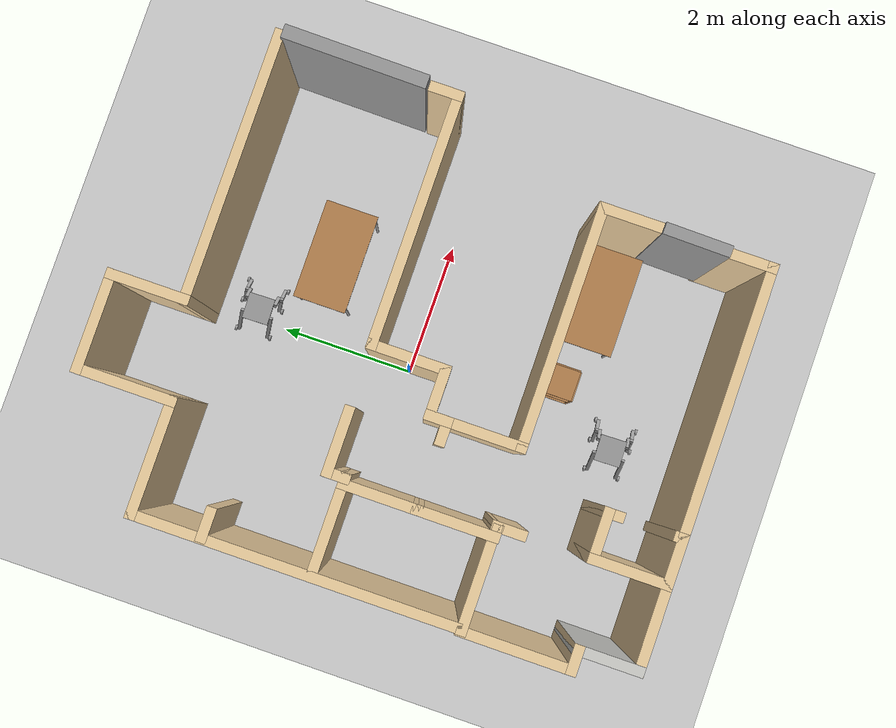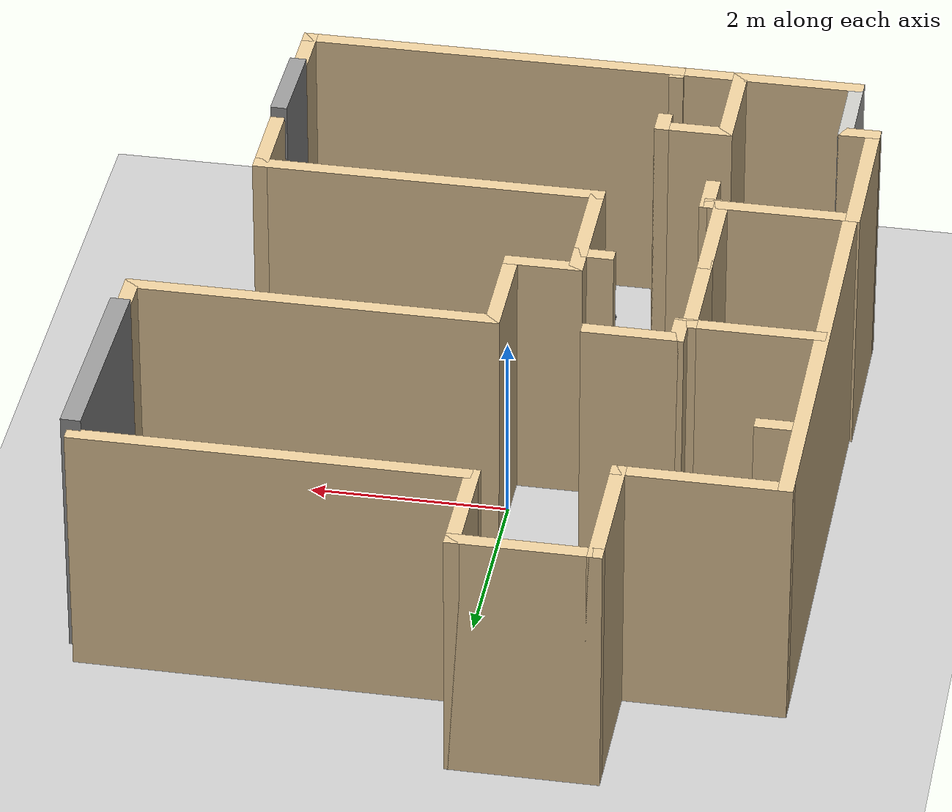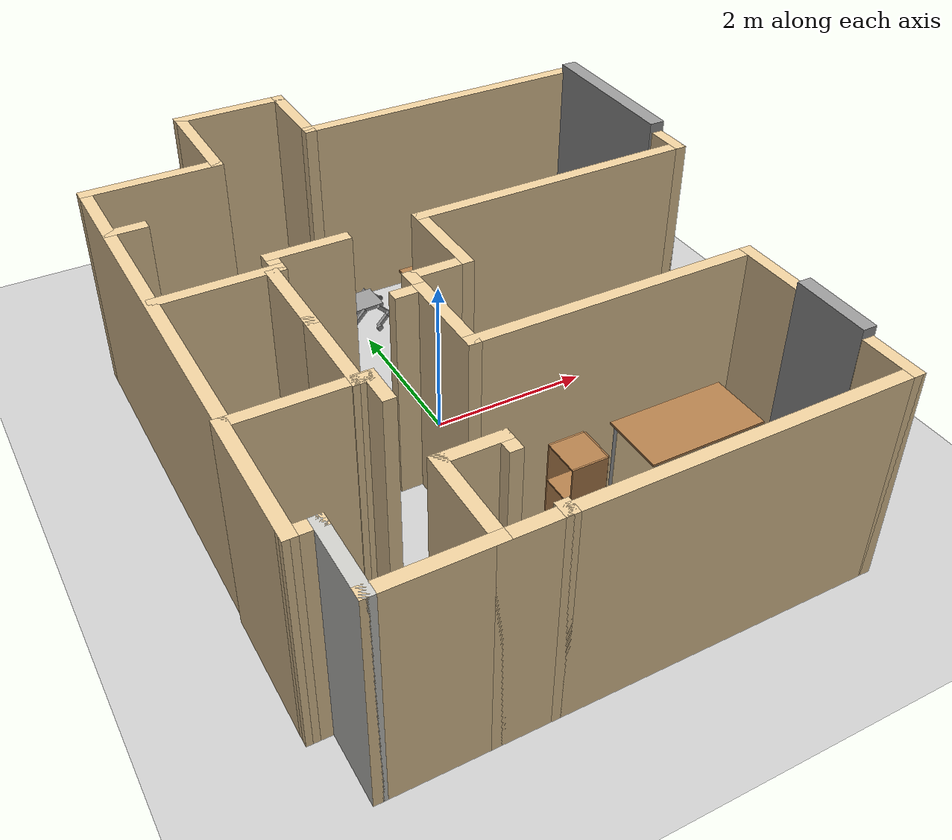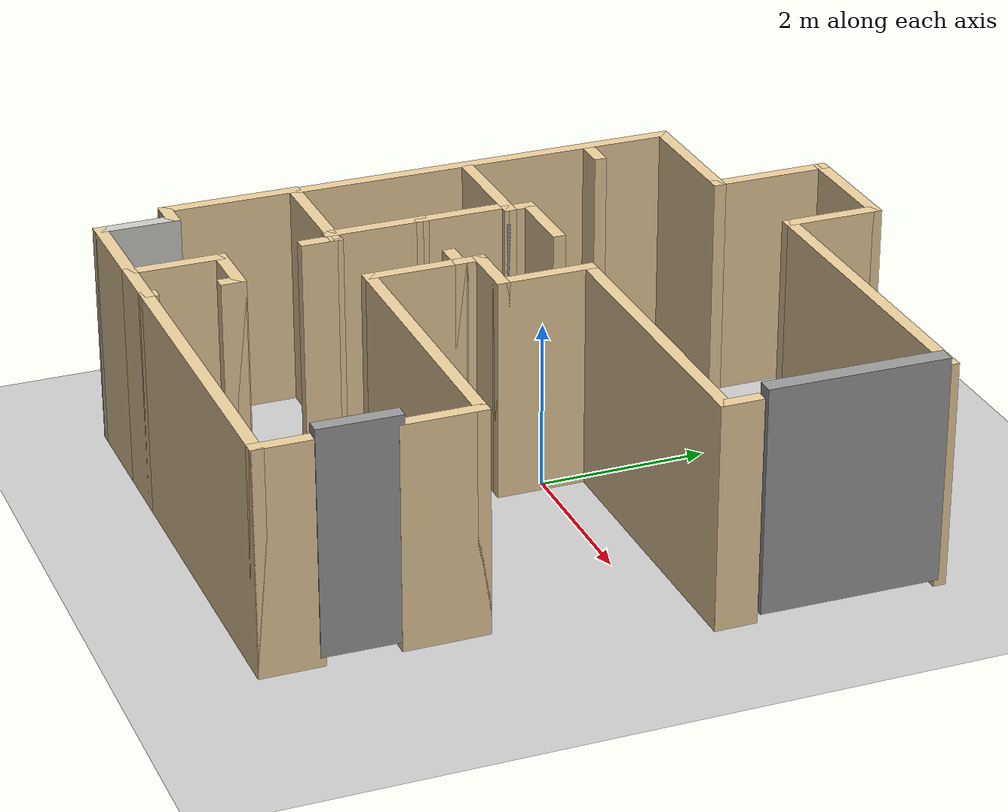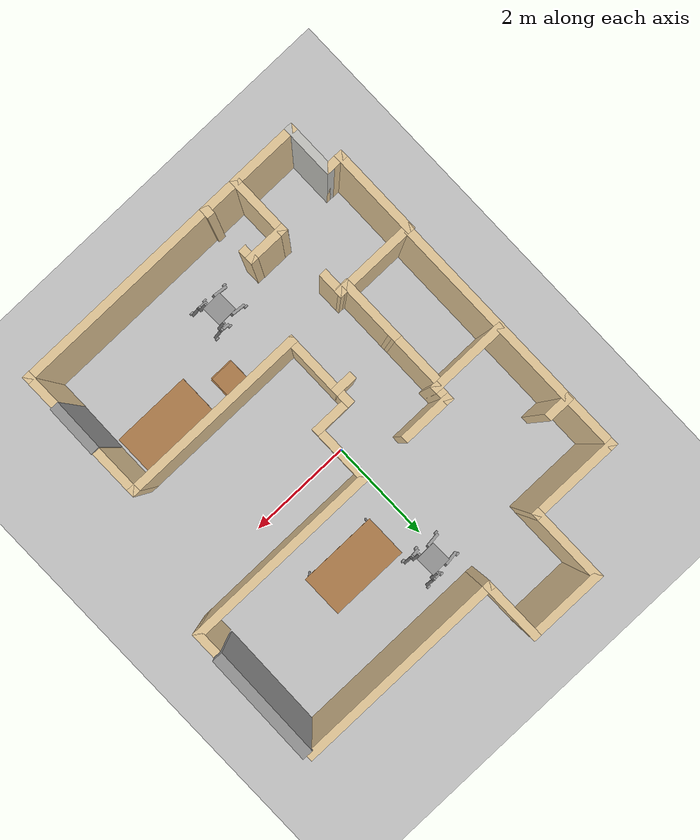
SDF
<sdf version="1.6">
 <world name="default">
  <plugin name="welcome_message" filename="libwelcome_message.so"/>
  <light name="sun" type="directional">
   <pose>0 0 10 0 -0 0</pose>
   <diffuse>0.8 0.8 0.8 1</diffuse>
   <specular>0.2 0.2 0.2 1</specular>
   <attenuation>
    <range>1000</range>
    <constant>0.9</constant>
    <linear>0.01</linear>
    <quadratic>0.001</quadratic>
   </attenuation>
   <direction>-0.5 0.1 -0.9</direction>
  </light>
  <model name="ground_plane">
   <static>1</static>
   <link name="link">
    <collision name="collision">
     <geometry><plane><normal>0 0 1</normal><size>100 100</size></plane></geometry>
     <surface>
      <contact><collide_bitmask>65535</collide_bitmask></contact>
      <friction><ode><mu>100</mu><mu2>50</mu2></ode></friction>
     </surface>
    </collision>
    <visual name="visual">
     <cast_shadows>0</cast_shadows>
     <geometry><plane><normal>0 0 1</normal><size>100 100</size></plane></geometry>
     <material>
      <script><uri>file://media/materials/scripts/gazebo.material</uri><name>Gazebo/Grey</name></script>
     </material>
    </visual>
   </link>
  </model>
  <gravity>0 0 -9.8</gravity>
  <magnetic_field>6e-06 2.3e-05 -4.2e-05</magnetic_field>
  <atmosphere type="adiabatic"/>
  <physics name="default_physics" default="0" type="ode">
   <max_step_size>0.001</max_step_size>
   <real_time_factor>1</real_time_factor>
   <real_time_update_rate>1000</real_time_update_rate>
  </physics>
  <scene><ambient>0.4 0.4 0.4 1</ambient><background>0.7 0.7 0.7 1</background><shadows>1</shadows></scene>
  <audio><device>default</device></audio>
  <spherical_coordinates>
   <surface_model>EARTH_WGS84</surface_model>
   <latitude_deg>0</latitude_deg>
   <longitude_deg>0</longitude_deg>
   <elevation>0</elevation>
   <heading_deg>0</heading_deg>
  </spherical_coordinates>
  <model name="domitory_wall">
   <pose>0.24381 -0.034166 0 0 -0 0</pose>
   <link name="Wall_100">
    <collision name="Wall_100_Collision">
     <geometry><box><size>1.5 0.15 2.67</size></box></geometry>
     <pose>0 0 1.335 0 -0 0</pose>
    </collision>
    <visual name="Wall_100_Visual">
     <pose>0 0 1.335 0 -0 0</pose>
     <geometry><box><size>1.5 0.15 2.67</size></box></geometry>
     <material>
      <script><uri>file://media/materials/scripts/gazebo.material</uri><name>Gazebo/Grey</name></script>
      <ambient>0.921569 0.807843 0.615686 1</ambient>
     </material>
     <meta><layer>0</layer></meta>
    </visual>
    <pose>-2.67494 0.319 0 0 -0 3.14159</pose>
   </link>
   <link name="Wall_104">
    <collision name="Wall_104_Collision">
     <geometry><box><size>0.5 0.15 2.67</size></box></geometry>
     <pose>0 0 1.335 0 -0 0</pose>
    </collision>
    <visual name="Wall_104_Visual">
     <pose>0 0 1.335 0 -0 0</pose>
     <geometry><box><size>0.5 0.15 2.67</size></box></geometry>
     <material>
      <script><uri>file://media/materials/scripts/gazebo.material</uri><name>Gazebo/Grey</name></script>
      <ambient>0.921569 0.807843 0.615686 1</ambient>
     </material>
     <meta><layer>0</layer></meta>
    </visual>
    <pose>-3.19294 1.871 0 0 -0 0</pose>
   </link>
   <link name="Wall_106">
    <collision name="Wall_106_Collision">
     <geometry><box><size>0.5 0.15 2.67</size></box></geometry>
     <pose>0 0 1.335 0 -0 0</pose>
    </collision>
    <visual name="Wall_106_Visual">
     <pose>0 0 1.335 0 -0 0</pose>
     <geometry><box><size>0.5 0.15 2.67</size></box></geometry>
     <material>
      <script><uri>file://media/materials/scripts/gazebo.material</uri><name>Gazebo/Grey</name></script>
      <ambient>0.921569 0.807843 0.615686 1</ambient>
     </material>
     <meta><layer>0</layer></meta>
    </visual>
    <pose>3.41406 0.744 0 0 -0 1.5708</pose>
   </link>
   <link name="Wall_18">
    <collision name="Wall_18_Collision">
     <geometry><box><size>1.25 0.15 2.67</size></box></geometry>
     <pose>0 0 1.335 0 -0 0</pose>
    </collision>
    <visual name="Wall_18_Visual">
     <pose>0 0 1.335 0 -0 0</pose>
     <geometry><box><size>1.25 0.15 2.67</size></box></geometry>
     <material>
      <script><uri>file://media/materials/scripts/gazebo.material</uri><name>Gazebo/Grey</name></script>
      <ambient>0.921569 0.807843 0.615686 1</ambient>
     </material>
     <meta><layer>0</layer></meta>
    </visual>
    <pose>-2.08414 -1.281 0 0 -0 -1.57116</pose>
   </link>
   <link name="Wall_20">
    <collision name="Wall_20_Collision">
     <geometry><box><size>0.41996 0.15 2.67</size></box></geometry>
     <pose>0 0 1.335 0 -0 0</pose>
    </collision>
    <visual name="Wall_20_Visual">
     <pose>0 0 1.335 0 -0 0</pose>
     <geometry><box><size>0.41996 0.15 2.67</size></box></geometry>
     <material>
      <script><uri>file://media/materials/scripts/gazebo.material</uri><name>Gazebo/Grey</name></script>
      <ambient>0.921569 0.807843 0.615686 1</ambient>
     </material>
     <meta><layer>0</layer></meta>
    </visual>
    <pose>-0.971011 -0.730784 0 0 -0 -0.001598</pose>
   </link>
   <link name="Wall_22">
    <collision name="Wall_22_Collision">
     <geometry><box><size>0.25 0.15 2.67</size></box></geometry>
     <pose>0 0 1.335 0 -0 0</pose>
    </collision>
    <visual name="Wall_22_Visual">
     <pose>0 0 1.335 0 -0 0</pose>
     <geometry><box><size>0.25 0.15 2.67</size></box></geometry>
     <material>
      <script><uri>file://media/materials/scripts/gazebo.material</uri><name>Gazebo/Grey</name></script>
      <ambient>0.921569 0.807843 0.615686 1</ambient>
     </material>
     <meta><layer>0</layer></meta>
    </visual>
    <pose>-2.03434 -1.831 0 0 -0 0</pose>
   </link>
   <link name="Wall_34">
    <collision name="Wall_34_Collision">
     <geometry><box><size>1.6 0.15 2.67</size></box></geometry>
     <pose>0 0 1.335 0 -0 0</pose>
    </collision>
    <visual name="Wall_34_Visual">
     <pose>0 0 1.335 0 -0 0</pose>
     <geometry><box><size>1.6 0.15 2.67</size></box></geometry>
     <material>
      <script><uri>file://media/materials/scripts/gazebo.material</uri><name>Gazebo/Grey</name></script>
      <ambient>0.921569 0.807843 0.615686 1</ambient>
     </material>
     <meta><layer>0</layer></meta>
    </visual>
    <pose>-2.66894 -1.81487 0 0 -0 3.14141</pose>
   </link>
   <link name="Wall_36">
    <collision name="Wall_36_Collision">
     <geometry><box><size>1.70427 0.15 2.67</size></box></geometry>
     <pose>0 0 1.335 0 -0 0</pose>
    </collision>
    <visual name="Wall_36_Visual">
     <pose>0 0 1.335 0 -0 0</pose>
     <geometry><box><size>1.70427 0.15 2.67</size></box></geometry>
     <material>
      <script><uri>file://media/materials/scripts/gazebo.material</uri><name>Gazebo/Grey</name></script>
      <ambient>0.921569 0.807843 0.615686 1</ambient>
     </material>
     <meta><layer>0</layer></meta>
    </visual>
    <pose>-3.41269 -2.59187 0 0 -0 -1.57241</pose>
   </link>
   <link name="Wall_38">
    <collision name="Wall_38_Collision">
     <geometry><box><size>0.43 0.15 2.67</size></box></geometry>
     <pose>0 0 1.335 0 -0 0</pose>
    </collision>
    <visual name="Wall_38_Visual">
     <pose>0 0 1.335 0 -0 0</pose>
     <geometry><box><size>0.43 0.15 2.67</size></box></geometry>
     <material>
      <script><uri>file://media/materials/scripts/gazebo.material</uri><name>Gazebo/Grey</name></script>
      <ambient>0.921569 0.807843 0.615686 1</ambient>
     </material>
     <meta><layer>0</layer></meta>
    </visual>
    <pose>-3.27394 -3.369 0 0 -0 0</pose>
   </link>
   <link name="Wall_40">
    <collision name="Wall_40_Collision">
     <geometry><box><size>1 0.15 2.67</size></box></geometry>
     <pose>0 0 1.335 0 -0 0</pose>
    </collision>
    <visual name="Wall_40_Visual">
     <pose>0 0 1.335 0 -0 0</pose>
     <geometry><box><size>1 0.15 2.67</size></box></geometry>
     <material>
      <script><uri>file://media/materials/scripts/gazebo.material</uri><name>Gazebo/CeilingTiled</name></script>
      <ambient>0.921569 0.807843 0.615686 1</ambient>
     </material>
     <meta><layer>0</layer></meta>
    </visual>
    <pose>-3.13394 -3.794 0 0 -0 -1.5708</pose>
   </link>
   <link name="Wall_42">
    <collision name="Wall_42_Collision">
     <geometry><box><size>0.5 0.15 2.67</size></box></geometry>
     <pose>0 0 1.335 0 -0 0</pose>
    </collision>
    <visual name="Wall_42_Visual">
     <pose>0 0 1.335 0 -0 0</pose>
     <geometry><box><size>0.5 0.15 2.67</size></box></geometry>
     <material>
      <script><uri>file://media/materials/scripts/gazebo.material</uri><name>Gazebo/Grey</name></script>
      <ambient>0.921569 0.807843 0.615686 1</ambient>
     </material>
     <meta><layer>0</layer></meta>
    </visual>
    <pose>-1.94394 -1.99 0 0 -0 -1.5708</pose>
   </link>
   <link name="Wall_44">
    <collision name="Wall_44_Collision">
     <geometry><box><size>1.35 0.15 2.67</size></box></geometry>
     <pose>0 0 1.335 0 -0 0</pose>
    </collision>
    <visual name="Wall_44_Visual">
     <pose>0 0 1.335 0 -0 0</pose>
     <geometry><box><size>1.35 0.15 2.67</size></box></geometry>
     <material>
      <script><uri>file://media/materials/scripts/gazebo.material</uri><name>Gazebo/Grey</name></script>
      <ambient>0.921569 0.807843 0.615686 1</ambient>
     </material>
     <meta><layer>0</layer></meta>
    </visual>
    <pose>-2.53394 -4.219 0 0 -0 0</pose>
   </link>
   <link name="Wall_48">
    <collision name="Wall_48_Collision">
     <geometry><box><size>1.2 0.15 2.67</size></box></geometry>
     <pose>0 0 1.335 0 -0 0</pose>
    </collision>
    <visual name="Wall_48_Visual">
     <pose>0 0 1.335 0 -0 0</pose>
     <geometry><box><size>1.2 0.15 2.67</size></box></geometry>
     <material>
      <script><uri>file://media/materials/scripts/gazebo.material</uri><name>Gazebo/Grey</name></script>
      <ambient>0.921569 0.807843 0.615686 1</ambient>
     </material>
     <meta><layer>0</layer></meta>
    </visual>
    <pose>-1.93394 -3.694 0 0 -0 1.5708</pose>
   </link>
   <link name="Wall_50">
    <collision name="Wall_50_Collision">
     <geometry><box><size>0.8 0.15 2.67</size></box></geometry>
     <pose>0 0 1.335 0 -0 0</pose>
    </collision>
    <visual name="Wall_50_Visual">
     <pose>0 0 1.335 0 -0 0</pose>
     <geometry><box><size>0.8 0.15 2.67</size></box></geometry>
     <material>
      <script><uri>file://media/materials/scripts/gazebo.material</uri><name>Gazebo/Grey</name></script>
      <ambient>0.921569 0.807843 0.615686 1</ambient>
     </material>
     <meta><layer>0</layer></meta>
    </visual>
    <pose>-1.60894 -4.219 0 0 -0 0</pose>
   </link>
   <link name="Wall_52">
    <collision name="Wall_52_Collision">
     <geometry><box><size>0.8 0.15 2.67</size></box></geometry>
     <pose>0 0 1.335 0 -0 0</pose>
    </collision>
    <visual name="Wall_52_Visual">
     <pose>0 0 1.335 0 -0 0</pose>
     <geometry><box><size>0.8 0.15 2.67</size></box></geometry>
     <material>
      <script><uri>file://media/materials/scripts/gazebo.material</uri><name>Gazebo/Grey</name></script>
      <ambient>0.921569 0.807843 0.615686 1</ambient>
     </material>
     <meta><layer>0</layer></meta>
    </visual>
    <pose>-1.60894 -3.169 0 0 -0 0</pose>
   </link>
   <link name="Wall_54">
    <collision name="Wall_54_Collision">
     <geometry><box><size>0.3 0.15 2.67</size></box></geometry>
     <pose>0 0 1.335 0 -0 0</pose>
    </collision>
    <visual name="Wall_54_Visual">
     <pose>0 0 1.335 0 -0 0</pose>
     <geometry><box><size>0.3 0.15 2.67</size></box></geometry>
     <material>
      <script><uri>file://media/materials/scripts/gazebo.material</uri><name>Gazebo/Grey</name></script>
      <ambient>0.921569 0.807843 0.615686 1</ambient>
     </material>
     <meta><layer>0</layer></meta>
    </visual>
    <pose>-1.28394 -3.244 0 0 -0 -1.5708</pose>
   </link>
   <link name="Wall_56">
    <collision name="Wall_56_Collision">
     <geometry><box><size>0.2 0.15 2.67</size></box></geometry>
     <pose>0 0 1.335 0 -0 0</pose>
    </collision>
    <visual name="Wall_56_Visual">
     <pose>0 0 1.335 0 -0 0</pose>
     <geometry><box><size>0.2 0.15 2.67</size></box></geometry>
     <material>
      <script><uri>file://media/materials/scripts/gazebo.material</uri><name>Gazebo/Grey</name></script>
      <ambient>0.921569 0.807843 0.615686 1</ambient>
     </material>
     <meta><layer>0</layer></meta>
    </visual>
    <pose>-1.28394 -4.194 0 0 -0 1.5708</pose>
   </link>
   <link name="Wall_58">
    <collision name="Wall_58_Collision">
     <geometry><box><size>4 0.15 2.67</size></box></geometry>
     <pose>0 0 1.335 0 -0 0</pose>
    </collision>
    <visual name="Wall_58_Visual">
     <pose>0 0 1.335 0 -0 0</pose>
     <geometry><box><size>4 0.15 2.67</size></box></geometry>
     <material>
      <script><uri>file://media/materials/scripts/gazebo.material</uri><name>Gazebo/Grey</name></script>
      <ambient>0.921569 0.807843 0.615686 1</ambient>
     </material>
     <meta><layer>0</layer></meta>
    </visual>
    <pose>0.641061 -4.219 0 0 -0 0</pose>
   </link>
   <link name="Wall_60">
    <collision name="Wall_60_Collision">
     <geometry><box><size>0.75 0.15 2.67</size></box></geometry>
     <pose>0 0 1.335 0 -0 0</pose>
    </collision>
    <visual name="Wall_60_Visual">
     <pose>0 0 1.335 0 -0 0</pose>
     <geometry><box><size>0.75 0.15 2.67</size></box></geometry>
     <material>
      <script><uri>file://media/materials/scripts/gazebo.material</uri><name>Gazebo/Grey</name></script>
      <ambient>0.921569 0.807843 0.615686 1</ambient>
     </material>
     <meta><layer>0</layer></meta>
    </visual>
    <pose>2.56606 -3.919 0 0 -0 1.5708</pose>
   </link>
   <link name="Wall_62">
    <collision name="Wall_62_Collision">
     <geometry><box><size>1 0.15 2.67</size></box></geometry>
     <pose>0 0 1.335 0 -0 0</pose>
    </collision>
    <visual name="Wall_62_Visual">
     <pose>0 0 1.335 0 -0 0</pose>
     <geometry><box><size>1 0.15 2.67</size></box></geometry>
     <material>
      <script><uri>file://media/materials/scripts/gazebo.material</uri><name>Gazebo/Grey</name></script>
      <ambient>0.921569 0.807843 0.615686 1</ambient>
     </material>
     <meta><layer>0</layer></meta>
    </visual>
    <pose>2.59406 -2.215 0 0 -0 1.5708</pose>
   </link>
   <link name="Wall_64">
    <collision name="Wall_64_Collision">
     <geometry><box><size>3.58 0.15 2.67</size></box></geometry>
     <pose>0 0 1.335 0 -0 0</pose>
    </collision>
    <visual name="Wall_64_Visual">
     <pose>0 0 1.335 0 -0 0</pose>
     <geometry><box><size>3.58 0.15 2.67</size></box></geometry>
     <material>
      <script><uri>file://media/materials/scripts/gazebo.material</uri><name>Gazebo/Grey</name></script>
      <ambient>0.921569 0.807843 0.615686 1</ambient>
     </material>
     <meta><layer>0</layer></meta>
    </visual>
    <pose>0.879061 -1.79 0 0 -0 3.14159</pose>
   </link>
   <link name="Wall_69">
    <collision name="Wall_69_Collision">
     <geometry><box><size>1.20986 0.15 2.67</size></box></geometry>
     <pose>0 0 1.335 0 -0 0</pose>
    </collision>
    <visual name="Wall_69_Visual">
     <pose>0 0 1.335 0 -0 0</pose>
     <geometry><box><size>1.20986 0.15 2.67</size></box></geometry>
     <material>
      <script><uri>file://media/materials/scripts/gazebo.material</uri><name>Gazebo/Grey</name></script>
      <ambient>0.921569 0.807843 0.615686 1</ambient>
     </material>
     <meta><layer>0</layer></meta>
    </visual>
    <pose>-0.83594 -1.2605 0 0 -0 -1.5708</pose>
   </link>
   <link name="Wall_71">
    <collision name="Wall_71_Collision">
     <geometry><box><size>1.2 0.15 2.67</size></box></geometry>
     <pose>0 0 1.335 0 -0 0</pose>
    </collision>
    <visual name="Wall_71_Visual">
     <pose>0 0 1.335 0 -0 0</pose>
     <geometry><box><size>1.2 0.15 2.67</size></box></geometry>
     <material>
      <script><uri>file://media/materials/scripts/gazebo.material</uri><name>Gazebo/Grey</name></script>
      <ambient>0.921569 0.807843 0.615686 1</ambient>
     </material>
     <meta><layer>0</layer></meta>
    </visual>
    <pose>-2.08394 -0.206 0 0 -0 1.5708</pose>
   </link>
   <link name="Wall_73">
    <collision name="Wall_73_Collision">
     <geometry><box><size>0.234 0.15 2.5</size></box></geometry>
     <pose>0 0 1.25 0 -0 0</pose>
    </collision>
    <visual name="Wall_73_Visual">
     <pose>0 0 1.25 0 -0 0</pose>
     <geometry><box><size>0.234 0.15 2.5</size></box></geometry>
     <material>
      <script><uri>file://media/materials/scripts/gazebo.material</uri><name>Gazebo/Grey</name></script>
      <ambient>1 1 1 1</ambient>
     </material>
     <meta><layer>0</layer></meta>
    </visual>
    <pose>-2.04194 0.319 0 0 -0 0</pose>
   </link>
   <link name="Wall_74">
    <collision name="Wall_74_Collision">
     <geometry><box><size>0.4 0.15 2.67</size></box></geometry>
     <pose>0 0 1.335 0 -0 0</pose>
    </collision>
    <visual name="Wall_74_Visual">
     <pose>0 0 1.335 0 -0 0</pose>
     <geometry><box><size>0.4 0.15 2.67</size></box></geometry>
     <material>
      <script><uri>file://media/materials/scripts/gazebo.material</uri><name>Gazebo/Grey</name></script>
      <ambient>0.921569 0.807843 0.615686 1</ambient>
     </material>
     <meta><layer>0</layer></meta>
    </visual>
    <pose>-1.99994 0.444 0 0 -0 1.5708</pose>
   </link>
   <link name="Wall_78">
    <collision name="Wall_78_Collision">
     <geometry><box><size>1.0156 0.15 2.67</size></box></geometry>
     <pose>0 0 1.335 0 -0 0</pose>
    </collision>
    <visual name="Wall_78_Visual">
     <pose>0 0 1.335 0 -0 0</pose>
     <geometry><box><size>1.0156 0.15 2.67</size></box></geometry>
     <material>
      <script><uri>file://media/materials/scripts/gazebo.material</uri><name>Gazebo/Grey</name></script>
      <ambient>0.921569 0.807843 0.615686 1</ambient>
     </material>
     <meta><layer>0</layer></meta>
    </visual>
    <pose>-1.56694 0.569 0 0 -0 0</pose>
   </link>
   <link name="Wall_80">
    <collision name="Wall_80_Collision">
     <geometry><box><size>0.4 0.15 2.67</size></box></geometry>
     <pose>0 0 1.335 0 -0 0</pose>
    </collision>
    <visual name="Wall_80_Visual">
     <pose>0 0 1.335 0 -0 0</pose>
     <geometry><box><size>0.4 0.15 2.67</size></box></geometry>
     <material>
      <script><uri>file://media/materials/scripts/gazebo.material</uri><name>Gazebo/Grey</name></script>
      <ambient>0.921569 0.807843 0.615686 1</ambient>
     </material>
     <meta><layer>0</layer></meta>
    </visual>
    <pose>-0.83594 -0.606 0 0 -0 1.5708</pose>
   </link>
   <link name="Wall_82">
    <collision name="Wall_82_Collision">
     <geometry><box><size>0.8 0.15 2.67</size></box></geometry>
     <pose>0 0 1.335 0 -0 0</pose>
    </collision>
    <visual name="Wall_82_Visual">
     <pose>0 0 1.335 0 -0 0</pose>
     <geometry><box><size>0.8 0.15 2.67</size></box></geometry>
     <material>
      <script><uri>file://media/materials/scripts/gazebo.material</uri><name>Gazebo/Grey</name></script>
      <ambient>0.921569 0.807843 0.615686 1</ambient>
     </material>
     <meta><layer>0</layer></meta>
    </visual>
    <pose>-0.510939 -0.481 0 0 -0 0</pose>
   </link>
   <link name="Wall_84">
    <collision name="Wall_84_Collision">
     <geometry><box><size>1.2 0.15 2.67</size></box></geometry>
     <pose>0 0 1.335 0 -0 0</pose>
    </collision>
    <visual name="Wall_84_Visual">
     <pose>0 0 1.335 0 -0 0</pose>
     <geometry><box><size>1.2 0.15 2.67</size></box></geometry>
     <material>
      <script><uri>file://media/materials/scripts/gazebo.material</uri><name>Gazebo/Grey</name></script>
      <ambient>0.921569 0.807843 0.615686 1</ambient>
     </material>
     <meta><layer>0</layer></meta>
    </visual>
    <pose>-0.185939 0.044 0 0 -0 1.5708</pose>
   </link>
   <link name="Wall_86">
    <collision name="Wall_86_Collision">
     <geometry><box><size>3.75 0.15 2.67</size></box></geometry>
     <pose>0 0 1.335 0 -0 0</pose>
    </collision>
    <visual name="Wall_86_Visual">
     <pose>0 0 1.335 0 -0 0</pose>
     <geometry><box><size>3.75 0.15 2.67</size></box></geometry>
     <material>
      <script><uri>file://media/materials/scripts/gazebo.material</uri><name>Gazebo/Grey</name></script>
      <ambient>0.921569 0.807843 0.615686 1</ambient>
     </material>
     <meta><layer>0</layer></meta>
    </visual>
    <pose>1.61406 0.569 0 0 -0 0</pose>
   </link>
   <link name="Wall_89">
    <collision name="Wall_89_Collision">
     <geometry><box><size>4 0.15 2.67</size></box></geometry>
     <pose>0 0 1.335 0 -0 0</pose>
    </collision>
    <visual name="Wall_89_Visual">
     <pose>0 0 1.335 0 -0 0</pose>
     <geometry><box><size>4 0.15 2.67</size></box></geometry>
     <material>
      <script><uri>file://media/materials/scripts/gazebo.material</uri><name>Gazebo/Grey</name></script>
      <ambient>0.921569 0.807843 0.615686 1</ambient>
     </material>
     <meta><layer>0</layer></meta>
    </visual>
    <pose>1.48906 3.169 0 0 -0 3.14159</pose>
   </link>
   <link name="Wall_90">
    <collision name="Wall_90_Collision">
     <geometry><box><size>1.2 0.15 2.67</size></box></geometry>
     <pose>0 0 1.335 0 -0 0</pose>
    </collision>
    <visual name="Wall_90_Visual">
     <pose>0 0 1.335 0 -0 0</pose>
     <geometry><box><size>1.2 0.15 2.67</size></box></geometry>
     <material>
      <script><uri>file://media/materials/scripts/gazebo.material</uri><name>Gazebo/Grey</name></script>
      <ambient>0.921569 0.807843 0.615686 1</ambient>
     </material>
     <meta><layer>0</layer></meta>
    </visual>
    <pose>-0.435939 3.694 0 0 -0 1.5708</pose>
   </link>
   <link name="Wall_92">
    <collision name="Wall_92_Collision">
     <geometry><box><size>1.5 0.15 2.67</size></box></geometry>
     <pose>0 0 1.335 0 -0 0</pose>
    </collision>
    <visual name="Wall_92_Visual">
     <pose>0 0 1.335 0 -0 0</pose>
     <geometry><box><size>1.5 0.15 2.67</size></box></geometry>
     <material>
      <script><uri>file://media/materials/scripts/gazebo.material</uri><name>Gazebo/Grey</name></script>
      <ambient>0.921569 0.807843 0.615686 1</ambient>
     </material>
     <meta><layer>0</layer></meta>
    </visual>
    <pose>-1.11094 4.219 0 0 -0 3.14159</pose>
   </link>
   <link name="Wall_93">
    <collision name="Wall_93_Collision">
     <geometry><box><size>1.5 0.15 2.67</size></box></geometry>
     <pose>0 0 1.335 0 -0 0</pose>
    </collision>
    <visual name="Wall_93_Visual">
     <pose>0 0 1.335 0 -0 0</pose>
     <geometry><box><size>1.5 0.15 2.67</size></box></geometry>
     <material>
      <script><uri>file://media/materials/scripts/gazebo.material</uri><name>Gazebo/Grey</name></script>
      <ambient>0.921569 0.807843 0.615686 1</ambient>
     </material>
     <meta><layer>0</layer></meta>
    </visual>
    <pose>-1.78594 3.544 0 0 -0 -1.5708</pose>
   </link>
   <link name="Wall_94">
    <collision name="Wall_94_Collision">
     <geometry><box><size>1.75 0.15 2.67</size></box></geometry>
     <pose>0 0 1.335 0 -0 0</pose>
    </collision>
    <visual name="Wall_94_Visual">
     <pose>0 0 1.335 0 -0 0</pose>
     <geometry><box><size>1.75 0.15 2.67</size></box></geometry>
     <material>
      <script><uri>file://media/materials/scripts/gazebo.material</uri><name>Gazebo/Grey</name></script>
      <ambient>0.921569 0.807843 0.615686 1</ambient>
     </material>
     <meta><layer>0</layer></meta>
    </visual>
    <pose>-2.58594 2.869 0 0 -0 3.14159</pose>
   </link>
   <link name="Wall_96">
    <collision name="Wall_96_Collision">
     <geometry><box><size>4.75 0.15 2.67</size></box></geometry>
     <pose>0 0 1.335 0 -0 0</pose>
    </collision>
    <visual name="Wall_96_Visual">
     <pose>0 0 1.335 0 -0 0</pose>
     <geometry><box><size>4.75 0.15 2.67</size></box></geometry>
     <material>
      <script><uri>file://media/materials/scripts/gazebo.material</uri><name>Gazebo/Grey</name></script>
      <ambient>0.921569 0.807843 0.615686 1</ambient>
     </material>
     <meta><layer>0</layer></meta>
    </visual>
    <pose>-3.38594 0.569 0 0 -0 -1.5708</pose>
   </link>
   <link name="Window_0">
    <collision name="Window_0_Collision">
     <geometry><box><size>0.96 0.17 2.67</size></box></geometry>
     <pose>0 0 0.95 0 -0 0</pose>
    </collision>
    <visual name="Window_0_Visual">
     <pose>0 0 0.95 0 -0 0</pose>
     <geometry><box><size>0.96 0.17 2.67</size></box></geometry>
     <material>
      <script><uri>file://media/materials/scripts/gazebo.material</uri><name>Gazebo/Grey</name></script>
     </material>
    </visual>
    <pose>2.57626 -3.12933 0.5 0 -0 1.55517</pose>
   </link>
   <link name="Window_1">
    <collision name="Window_1_Collision">
     <geometry><box><size>2.1 0.2 2.67</size></box></geometry>
     <pose>0 0 0.95 0 -0 0</pose>
    </collision>
    <visual name="Window_1_Visual">
     <pose>0 0 0.95 0 -0 0</pose>
     <geometry><box><size>2.1 0.2 2.67</size></box></geometry>
     <material>
      <script><uri>file://media/materials/scripts/gazebo.material</uri><name>Gazebo/Grey</name></script>
     </material>
    </visual>
    <pose>3.43737 2.06548 0.5 0 -0 1.55727</pose>
   </link>
   <static>1</static>
  </model>
  <model name="cabinet">
   <static>1</static>
   <link name="cabinet_bottom_plate">
    <inertial>
     <pose>0 0 -1 0 -0 0</pose>
     <inertia><ixx>2.05</ixx><ixy>0</ixy><ixz>0</ixz><iyy>2.05</iyy><iyz>0</iyz><izz>2.05</izz></inertia>
     <mass>25</mass>
    </inertial>
    <collision name="cabinet_bottom_plate_geom">
     <pose>0 0 0.01 0 -0 0</pose>
     <geometry><box><size>0.45 0.45 0.02</size></box></geometry>
    </collision>
    <visual name="cabinet_bottom_plate_geom_visual">
     <pose>0 0 0.01 0 -0 0</pose>
     <geometry><box><size>0.45 0.45 0.02</size></box></geometry>
     <material>
      <script><uri>file://media/materials/scripts/gazebo.material</uri><name>Gazebo/Wood</name></script>
     </material>
    </visual>
    <collision name="cabinet_bottom_plate_geom_cabinet_back_plate">
     <pose>0.235 0 0.51 0 -0 0</pose>
     <geometry><box><size>0.02 0.45 1.02</size></box></geometry>
    </collision>
    <visual name="cabinet_bottom_plate_geom_cabinet_back_plate_visual">
     <pose>0.235 0 0.51 0 -0 0</pose>
     <geometry><box><size>0.02 0.45 1.02</size></box></geometry>
     <material>
      <script><uri>file://media/materials/scripts/gazebo.material</uri><name>Gazebo/Wood</name></script>
     </material>
    </visual>
    <collision name="cabinet_bottom_plate_geom_cabinet_left_plate">
     <pose>0 0.235 0.51 0 -0 0</pose>
     <geometry><box><size>0.45 0.02 1.02</size></box></geometry>
    </collision>
    <visual name="cabinet_bottom_plate_geom_cabinet_left_plate_visual">
     <pose>0 0.235 0.51 0 -0 0</pose>
     <geometry><box><size>0.45 0.02 1.02</size></box></geometry>
     <material>
      <script><uri>file://media/materials/scripts/gazebo.material</uri><name>Gazebo/Wood</name></script>
     </material>
    </visual>
    <collision name="cabinet_bottom_plate_geom_cabinet_middle_plate">
     <pose>0 0 0.51 0 -0 0</pose>
     <geometry><box><size>0.45 0.45 0.02</size></box></geometry>
    </collision>
    <visual name="cabinet_bottom_plate_geom_cabinet_middle_plate_visual">
     <pose>0 0 0.51 0 -0 0</pose>
     <geometry><box><size>0.45 0.45 0.02</size></box></geometry>
     <material>
      <script><uri>file://media/materials/scripts/gazebo.material</uri><name>Gazebo/Wood</name></script>
     </material>
    </visual>
    <collision name="cabinet_bottom_plate_geom_cabinet_right_plate">
     <pose>0 -0.235 0.51 0 -0 0</pose>
     <geometry><box><size>0.45 0.02 1.02</size></box></geometry>
    </collision>
    <visual name="cabinet_bottom_plate_geom_cabinet_right_plate_visual">
     <pose>0 -0.235 0.51 0 -0 0</pose>
     <geometry><box><size>0.45 0.02 1.02</size></box></geometry>
     <material>
      <script><uri>file://media/materials/scripts/gazebo.material</uri><name>Gazebo/Wood</name></script>
     </material>
    </visual>
    <collision name="cabinet_bottom_plate_geom_cabinet_top_plate">
     <pose>0 0 1.01 0 -0 0</pose>
     <geometry><box><size>0.45 0.45 0.02</size></box></geometry>
    </collision>
    <visual name="cabinet_bottom_plate_geom_cabinet_top_plate_visual">
     <pose>0 0 1.01 0 -0 0</pose>
     <geometry><box><size>0.45 0.45 0.02</size></box></geometry>
     <material>
      <script><uri>file://media/materials/scripts/gazebo.material</uri><name>Gazebo/Wood</name></script>
     </material>
    </visual>
   </link>
   <pose>0.539238 -2.16083 0 0 -0 0</pose>
  </model>
  <model name="table">
   <static>1</static>
   <link name="link">
    <collision name="surface">
     <pose>0 0 1 0 -0 0</pose>
     <geometry><box><size>1.5 0.8 0.03</size></box></geometry>
     <surface><friction><ode><mu>0.6</mu><mu2>0.6</mu2></ode></friction></surface>
    </collision>
    <visual name="visual1">
     <pose>0 0 1 0 -0 0</pose>
     <geometry><box><size>1.5 0.8 0.03</size></box></geometry>
     <material>
      <script><uri>file://media/materials/scripts/gazebo.material</uri><name>Gazebo/Wood</name></script>
     </material>
    </visual>
    <collision name="front_left_leg">
     <pose>0.68 0.38 0.5 0 -0 0</pose>
     <geometry><cylinder><radius>0.02</radius><length>1</length></cylinder></geometry>
    </collision>
    <visual name="front_left_leg">
     <pose>0.68 0.38 0.5 0 -0 0</pose>
     <geometry><cylinder><radius>0.02</radius><length>1</length></cylinder></geometry>
     <material>
      <script><uri>file://media/materials/scripts/gazebo.material</uri><name>Gazebo/Grey</name></script>
     </material>
    </visual>
    <collision name="front_right_leg">
     <pose>0.68 -0.38 0.5 0 -0 0</pose>
     <geometry><cylinder><radius>0.02</radius><length>1</length></cylinder></geometry>
    </collision>
    <visual name="front_right_leg">
     <pose>0.68 -0.38 0.5 0 -0 0</pose>
     <geometry><cylinder><radius>0.02</radius><length>1</length></cylinder></geometry>
     <material>
      <script><uri>file://media/materials/scripts/gazebo.material</uri><name>Gazebo/Grey</name></script>
     </material>
    </visual>
    <collision name="back_right_leg">
     <pose>-0.68 -0.38 0.5 0 -0 0</pose>
     <geometry><cylinder><radius>0.02</radius><length>1</length></cylinder></geometry>
    </collision>
    <visual name="back_right_leg">
     <pose>-0.68 -0.38 0.5 0 -0 0</pose>
     <geometry><cylinder><radius>0.02</radius><length>1</length></cylinder></geometry>
     <material>
      <script><uri>file://media/materials/scripts/gazebo.material</uri><name>Gazebo/Grey</name></script>
     </material>
    </visual>
    <collision name="back_left_leg">
     <pose>-0.68 0.38 0.5 0 -0 0</pose>
     <geometry><cylinder><radius>0.02</radius><length>1</length></cylinder></geometry>
    </collision>
    <visual name="back_left_leg">
     <pose>-0.68 0.38 0.5 0 -0 0</pose>
     <geometry><cylinder><radius>0.02</radius><length>1</length></cylinder></geometry>
     <material>
      <script><uri>file://media/materials/scripts/gazebo.material</uri><name>Gazebo/Grey</name></script>
     </material>
    </visual>
   </link>
   <pose>1.86359 -2.3274 0 0 -0 0</pose>
  </model>
  <model name="table_clone">
   <static>1</static>
   <link name="link">
    <collision name="surface">
     <pose>0 0 1 0 -0 0</pose>
     <geometry><box><size>1.5 0.8 0.03</size></box></geometry>
     <surface><friction><ode><mu>0.6</mu><mu2>0.6</mu2></ode></friction></surface>
    </collision>
    <visual name="visual1">
     <pose>0 0 1 0 -0 0</pose>
     <geometry><box><size>1.5 0.8 0.03</size></box></geometry>
     <material>
      <script><uri>file://media/materials/scripts/gazebo.material</uri><name>Gazebo/Wood</name></script>
     </material>
    </visual>
    <collision name="front_left_leg">
     <pose>0.68 0.38 0.5 0 -0 0</pose>
     <geometry><cylinder><radius>0.02</radius><length>1</length></cylinder></geometry>
    </collision>
    <visual name="front_left_leg">
     <pose>0.68 0.38 0.5 0 -0 0</pose>
     <geometry><cylinder><radius>0.02</radius><length>1</length></cylinder></geometry>
     <material>
      <script><uri>file://media/materials/scripts/gazebo.material</uri><name>Gazebo/Grey</name></script>
     </material>
    </visual>
    <collision name="front_right_leg">
     <pose>0.68 -0.38 0.5 0 -0 0</pose>
     <geometry><cylinder><radius>0.02</radius><length>1</length></cylinder></geometry>
    </collision>
    <visual name="front_right_leg">
     <pose>0.68 -0.38 0.5 0 -0 0</pose>
     <geometry><cylinder><radius>0.02</radius><length>1</length></cylinder></geometry>
     <material>
      <script><uri>file://media/materials/scripts/gazebo.material</uri><name>Gazebo/Grey</name></script>
     </material>
    </visual>
    <collision name="back_right_leg">
     <pose>-0.68 -0.38 0.5 0 -0 0</pose>
     <geometry><cylinder><radius>0.02</radius><length>1</length></cylinder></geometry>
    </collision>
    <visual name="back_right_leg">
     <pose>-0.68 -0.38 0.5 0 -0 0</pose>
     <geometry><cylinder><radius>0.02</radius><length>1</length></cylinder></geometry>
     <material>
      <script><uri>file://media/materials/scripts/gazebo.material</uri><name>Gazebo/Grey</name></script>
     </material>
    </visual>
    <collision name="back_left_leg">
     <pose>-0.68 0.38 0.5 0 -0 0</pose>
     <geometry><cylinder><radius>0.02</radius><length>1</length></cylinder></geometry>
    </collision>
    <visual name="back_left_leg">
     <pose>-0.68 0.38 0.5 0 -0 0</pose>
     <geometry><cylinder><radius>0.02</radius><length>1</length></cylinder></geometry>
     <material>
      <script><uri>file://media/materials/scripts/gazebo.material</uri><name>Gazebo/Grey</name></script>
     </material>
    </visual>
   </link>
   <pose>1.20278 1.55731 0 0 -0 0</pose>
  </model>
  <model name="robot_1">
   <plugin name="model_push" filename="libmodel_push.so"/>
   <link name="link_0_clone">
    <inertial>
     <mass>1</mass>
     <inertia>
      <ixx>0.166667</ixx>
      <ixy>0</ixy>
      <ixz>0</ixz>
      <iyy>0.166667</iyy>
      <iyz>0</iyz>
      <izz>0.166667</izz>
     </inertia>
    </inertial>
    <pose>-0.152134 0.868305 0 0 -0 0</pose>
    <visual name="visual">
     <geometry><box><size>0.4 0.4 0.05</size></box></geometry>
     <material>
      <lighting>1</lighting>
      <script><uri>file://media/materials/scripts/gazebo.material</uri><name>Gazebo/Grey</name></script>
      <shader type="vertex"><normal_map>__default__</normal_map></shader>
      <ambient>0.3 0.3 0.3 1</ambient>
      <diffuse>0.7 0.7 0.7 1</diffuse>
      <specular>0.01 0.01 0.01 1</specular>
      <emissive>0 0 0 1</emissive>
     </material>
    </visual>
    <collision name="collision">
     <geometry><box><size>0.4 0.4 0.05</size></box></geometry>
     <surface>
      <friction>
       <ode><mu>1</mu><mu2>1</mu2><fdir1>0 0 0</fdir1><slip1>0</slip1><slip2>0</slip2></ode>
       <torsional>
        <coefficient>1</coefficient>
        <patch_radius>0</patch_radius>
        <surface_radius>0</surface_radius>
        <use_patch_radius>1</use_patch_radius>
        <ode><slip>0</slip></ode>
       </torsional>
      </friction>
      <bounce><restitution_coefficient>0</restitution_coefficient><threshold>1e+06</threshold></bounce>
      <contact>
       <collide_without_contact>0</collide_without_contact>
       <collide_without_contact_bitmask>1</collide_without_contact_bitmask>
       <collide_bitmask>1</collide_bitmask>
       <ode>
        <soft_cfm>0</soft_cfm>
        <soft_erp>0.2</soft_erp>
        <kp>1e+13</kp>
        <kd>1</kd>
        <max_vel>0.01</max_vel>
        <min_depth>0</min_depth>
       </ode>
       <bullet>
        <split_impulse>1</split_impulse>
        <split_impulse_penetration_threshold>-0.01</split_impulse_penetration_threshold>
        <soft_cfm>0</soft_cfm>
        <soft_erp>0.2</soft_erp>
        <kp>1e+13</kp>
        <kd>1</kd>
       </bullet>
      </contact>
     </surface>
    </collision>
   </link>
   <link name="link_0_clone_0">
    <inertial>
     <mass>1</mass>
     <inertia><ixx>0.145833</ixx><ixy>0</ixy><ixz>0</ixz><iyy>0.145833</iyy><iyz>0</iyz><izz>0.125</izz></inertia>
    </inertial>
    <pose>-0.469634 1.26045 -0.272118 -1.565 1.55233 -1.56544</pose>
    <visual name="visual">
     <geometry><cylinder><radius>0.04</radius><length>0.035</length></cylinder></geometry>
     <material>
      <lighting>1</lighting>
      <script><uri>file://media/materials/scripts/gazebo.material</uri><name>Gazebo/Grey</name></script>
      <shader type="vertex"><normal_map>__default__</normal_map></shader>
      <ambient>0.3 0.3 0.3 1</ambient>
      <diffuse>0.7 0.7 0.7 1</diffuse>
      <specular>0.01 0.01 0.01 1</specular>
      <emissive>0 0 0 1</emissive>
     </material>
    </visual>
    <collision name="collision">
     <geometry><cylinder><radius>0.04</radius><length>0.035</length></cylinder></geometry>
     <surface>
      <friction>
       <ode><mu>1</mu><mu2>1</mu2><fdir1>0 0 0</fdir1><slip1>0</slip1><slip2>0</slip2></ode>
       <torsional>
        <coefficient>1</coefficient>
        <patch_radius>0</patch_radius>
        <surface_radius>0</surface_radius>
        <use_patch_radius>1</use_patch_radius>
        <ode><slip>0</slip></ode>
       </torsional>
      </friction>
      <bounce><restitution_coefficient>0</restitution_coefficient><threshold>1e+06</threshold></bounce>
      <contact>
       <collide_without_contact>0</collide_without_contact>
       <collide_without_contact_bitmask>1</collide_without_contact_bitmask>
       <collide_bitmask>1</collide_bitmask>
       <ode>
        <soft_cfm>0</soft_cfm>
        <soft_erp>0.2</soft_erp>
        <kp>1e+13</kp>
        <kd>1</kd>
        <max_vel>0.01</max_vel>
        <min_depth>0</min_depth>
       </ode>
       <bullet>
        <split_impulse>1</split_impulse>
        <split_impulse_penetration_threshold>-0.01</split_impulse_penetration_threshold>
        <soft_cfm>0</soft_cfm>
        <soft_erp>0.2</soft_erp>
        <kp>1e+13</kp>
        <kd>1</kd>
       </bullet>
      </contact>
     </surface>
    </collision>
   </link>
   <link name="link_0_clone_1">
    <inertial>
     <mass>1</mass>
     <inertia><ixx>0.145833</ixx><ixy>0</ixy><ixz>0</ixz><iyy>0.145833</iyy><iyz>0</iyz><izz>0.125</izz></inertia>
    </inertial>
    <pose>-0.469634 0.942191 -0.272047 -1.565 1.55233 -1.56544</pose>
    <visual name="visual">
     <geometry><cylinder><radius>0.04</radius><length>0.035</length></cylinder></geometry>
     <material>
      <lighting>1</lighting>
      <script><uri>file://media/materials/scripts/gazebo.material</uri><name>Gazebo/Grey</name></script>
      <shader type="vertex"><normal_map>__default__</normal_map></shader>
      <ambient>0.3 0.3 0.3 1</ambient>
      <diffuse>0.7 0.7 0.7 1</diffuse>
      <specular>0.01 0.01 0.01 1</specular>
      <emissive>0 0 0 1</emissive>
     </material>
    </visual>
    <collision name="collision">
     <geometry><cylinder><radius>0.04</radius><length>0.035</length></cylinder></geometry>
     <surface>
      <friction>
       <ode><mu>1</mu><mu2>1</mu2><fdir1>0 0 0</fdir1><slip1>0</slip1><slip2>0</slip2></ode>
       <torsional>
        <coefficient>1</coefficient>
        <patch_radius>0</patch_radius>
        <surface_radius>0</surface_radius>
        <use_patch_radius>1</use_patch_radius>
        <ode><slip>0</slip></ode>
       </torsional>
      </friction>
      <bounce><restitution_coefficient>0</restitution_coefficient><threshold>1e+06</threshold></bounce>
      <contact>
       <collide_without_contact>0</collide_without_contact>
       <collide_without_contact_bitmask>1</collide_without_contact_bitmask>
       <collide_bitmask>1</collide_bitmask>
       <ode>
        <soft_cfm>0</soft_cfm>
        <soft_erp>0.2</soft_erp>
        <kp>1e+13</kp>
        <kd>1</kd>
        <max_vel>0.01</max_vel>
        <min_depth>0</min_depth>
       </ode>
       <bullet>
        <split_impulse>1</split_impulse>
        <split_impulse_penetration_threshold>-0.01</split_impulse_penetration_threshold>
        <soft_cfm>0</soft_cfm>
        <soft_erp>0.2</soft_erp>
        <kp>1e+13</kp>
        <kd>1</kd>
       </bullet>
      </contact>
     </surface>
    </collision>
   </link>
   <link name="link_0_clone_2">
    <inertial>
     <mass>1</mass>
     <inertia><ixx>0.145833</ixx><ixy>0</ixy><ixz>0</ixz><iyy>0.145833</iyy><iyz>0</iyz><izz>0.125</izz></inertia>
    </inertial>
    <pose>0.165366 1.26045 -0.272118 -1.56501 1.55233 -1.56545</pose>
    <visual name="visual">
     <geometry><cylinder><radius>0.04</radius><length>0.035</length></cylinder></geometry>
     <material>
      <lighting>1</lighting>
      <script><uri>file://media/materials/scripts/gazebo.material</uri><name>Gazebo/Grey</name></script>
      <shader type="vertex"><normal_map>__default__</normal_map></shader>
      <ambient>0.3 0.3 0.3 1</ambient>
      <diffuse>0.7 0.7 0.7 1</diffuse>
      <specular>0.01 0.01 0.01 1</specular>
      <emissive>0 0 0 1</emissive>
     </material>
    </visual>
    <collision name="collision">
     <geometry><cylinder><radius>0.04</radius><length>0.035</length></cylinder></geometry>
     <surface>
      <friction>
       <ode><mu>1</mu><mu2>1</mu2><fdir1>0 0 0</fdir1><slip1>0</slip1><slip2>0</slip2></ode>
       <torsional>
        <coefficient>1</coefficient>
        <patch_radius>0</patch_radius>
        <surface_radius>0</surface_radius>
        <use_patch_radius>1</use_patch_radius>
        <ode><slip>0</slip></ode>
       </torsional>
      </friction>
      <bounce><restitution_coefficient>0</restitution_coefficient><threshold>1e+06</threshold></bounce>
      <contact>
       <collide_without_contact>0</collide_without_contact>
       <collide_without_contact_bitmask>1</collide_without_contact_bitmask>
       <collide_bitmask>1</collide_bitmask>
       <ode>
        <soft_cfm>0</soft_cfm>
        <soft_erp>0.2</soft_erp>
        <kp>1e+13</kp>
        <kd>1</kd>
        <max_vel>0.01</max_vel>
        <min_depth>0</min_depth>
       </ode>
       <bullet>
        <split_impulse>1</split_impulse>
        <split_impulse_penetration_threshold>-0.01</split_impulse_penetration_threshold>
        <soft_cfm>0</soft_cfm>
        <soft_erp>0.2</soft_erp>
        <kp>1e+13</kp>
        <kd>1</kd>
       </bullet>
      </contact>
     </surface>
    </collision>
   </link>
   <link name="link_0_clone_3">
    <inertial>
     <mass>1</mass>
     <inertia><ixx>0.145833</ixx><ixy>0</ixy><ixz>0</ixz><iyy>0.145833</iyy><iyz>0</iyz><izz>0.125</izz></inertia>
    </inertial>
    <pose>-0.419634 0.501827 -0.261365 -1.565 1.55233 -1.56544</pose>
    <visual name="visual">
     <geometry><cylinder><radius>0.04</radius><length>0.035</length></cylinder></geometry>
     <material>
      <lighting>1</lighting>
      <script><uri>file://media/materials/scripts/gazebo.material</uri><name>Gazebo/Grey</name></script>
      <shader type="vertex"><normal_map>__default__</normal_map></shader>
      <ambient>0.3 0.3 0.3 1</ambient>
      <diffuse>0.7 0.7 0.7 1</diffuse>
      <specular>0.01 0.01 0.01 1</specular>
      <emissive>0 0 0 1</emissive>
     </material>
    </visual>
    <collision name="collision">
     <geometry><cylinder><radius>0.04</radius><length>0.035</length></cylinder></geometry>
     <surface>
      <friction>
       <ode><mu>1</mu><mu2>1</mu2><fdir1>0 0 0</fdir1><slip1>0</slip1><slip2>0</slip2></ode>
       <torsional>
        <coefficient>1</coefficient>
        <patch_radius>0</patch_radius>
        <surface_radius>0</surface_radius>
        <use_patch_radius>1</use_patch_radius>
        <ode><slip>0</slip></ode>
       </torsional>
      </friction>
      <bounce><restitution_coefficient>0</restitution_coefficient><threshold>1e+06</threshold></bounce>
      <contact>
       <collide_without_contact>0</collide_without_contact>
       <collide_without_contact_bitmask>1</collide_without_contact_bitmask>
       <collide_bitmask>1</collide_bitmask>
       <ode>
        <soft_cfm>0</soft_cfm>
        <soft_erp>0.2</soft_erp>
        <kp>1e+13</kp>
        <kd>1</kd>
        <max_vel>0.01</max_vel>
        <min_depth>0</min_depth>
       </ode>
       <bullet>
        <split_impulse>1</split_impulse>
        <split_impulse_penetration_threshold>-0.01</split_impulse_penetration_threshold>
        <soft_cfm>0</soft_cfm>
        <soft_erp>0.2</soft_erp>
        <kp>1e+13</kp>
        <kd>1</kd>
       </bullet>
      </contact>
     </surface>
    </collision>
   </link>
   <link name="link_0_clone_4">
    <inertial>
     <mass>1</mass>
     <inertia><ixx>0.145833</ixx><ixy>0</ixy><ixz>0</ixz><iyy>0.145833</iyy><iyz>0</iyz><izz>0.125</izz></inertia>
    </inertial>
    <pose>0.165366 0.942191 -0.272048 -1.565 1.55233 -1.56544</pose>
    <visual name="visual">
     <geometry><cylinder><radius>0.04</radius><length>0.035</length></cylinder></geometry>
     <material>
      <lighting>1</lighting>
      <script><uri>file://media/materials/scripts/gazebo.material</uri><name>Gazebo/Grey</name></script>
      <shader type="vertex"><normal_map>__default__</normal_map></shader>
      <ambient>0.3 0.3 0.3 1</ambient>
      <diffuse>0.7 0.7 0.7 1</diffuse>
      <specular>0.01 0.01 0.01 1</specular>
      <emissive>0 0 0 1</emissive>
     </material>
    </visual>
    <collision name="collision">
     <geometry><cylinder><radius>0.04</radius><length>0.035</length></cylinder></geometry>
     <surface>
      <friction>
       <ode><mu>1</mu><mu2>1</mu2><fdir1>0 0 0</fdir1><slip1>0</slip1><slip2>0</slip2></ode>
       <torsional>
        <coefficient>1</coefficient>
        <patch_radius>0</patch_radius>
        <surface_radius>0</surface_radius>
        <use_patch_radius>1</use_patch_radius>
        <ode><slip>0</slip></ode>
       </torsional>
      </friction>
      <bounce><restitution_coefficient>0</restitution_coefficient><threshold>1e+06</threshold></bounce>
      <contact>
       <collide_without_contact>0</collide_without_contact>
       <collide_without_contact_bitmask>1</collide_without_contact_bitmask>
       <collide_bitmask>1</collide_bitmask>
       <ode>
        <soft_cfm>0</soft_cfm>
        <soft_erp>0.2</soft_erp>
        <kp>1e+13</kp>
        <kd>1</kd>
        <max_vel>0.01</max_vel>
        <min_depth>0</min_depth>
       </ode>
       <bullet>
        <split_impulse>1</split_impulse>
        <split_impulse_penetration_threshold>-0.01</split_impulse_penetration_threshold>
        <soft_cfm>0</soft_cfm>
        <soft_erp>0.2</soft_erp>
        <kp>1e+13</kp>
        <kd>1</kd>
       </bullet>
      </contact>
     </surface>
    </collision>
   </link>
   <link name="link_0_clone_5">
    <inertial>
     <mass>1</mass>
     <inertia><ixx>0.145833</ixx><ixy>0</ixy><ixz>0</ixz><iyy>0.145833</iyy><iyz>0</iyz><izz>0.125</izz></inertia>
    </inertial>
    <pose>0.115366 0.501827 -0.261365 -1.565 1.55233 -1.56544</pose>
    <visual name="visual">
     <geometry><cylinder><radius>0.04</radius><length>0.035</length></cylinder></geometry>
     <material>
      <lighting>1</lighting>
      <script><uri>file://media/materials/scripts/gazebo.material</uri><name>Gazebo/Grey</name></script>
      <shader type="vertex"><normal_map>__default__</normal_map></shader>
      <ambient>0.3 0.3 0.3 1</ambient>
      <diffuse>0.7 0.7 0.7 1</diffuse>
      <specular>0.01 0.01 0.01 1</specular>
      <emissive>0 0 0 1</emissive>
     </material>
    </visual>
    <collision name="collision">
     <geometry><cylinder><radius>0.04</radius><length>0.035</length></cylinder></geometry>
     <surface>
      <friction>
       <ode><mu>1</mu><mu2>1</mu2><fdir1>0 0 0</fdir1><slip1>0</slip1><slip2>0</slip2></ode>
       <torsional>
        <coefficient>1</coefficient>
        <patch_radius>0</patch_radius>
        <surface_radius>0</surface_radius>
        <use_patch_radius>1</use_patch_radius>
        <ode><slip>0</slip></ode>
       </torsional>
      </friction>
      <bounce><restitution_coefficient>0</restitution_coefficient><threshold>1e+06</threshold></bounce>
      <contact>
       <collide_without_contact>0</collide_without_contact>
       <collide_without_contact_bitmask>1</collide_without_contact_bitmask>
       <collide_bitmask>1</collide_bitmask>
       <ode>
        <soft_cfm>0</soft_cfm>
        <soft_erp>0.2</soft_erp>
        <kp>1e+13</kp>
        <kd>1</kd>
        <max_vel>0.01</max_vel>
        <min_depth>0</min_depth>
       </ode>
       <bullet>
        <split_impulse>1</split_impulse>
        <split_impulse_penetration_threshold>-0.01</split_impulse_penetration_threshold>
        <soft_cfm>0</soft_cfm>
        <soft_erp>0.2</soft_erp>
        <kp>1e+13</kp>
        <kd>1</kd>
       </bullet>
      </contact>
     </surface>
    </collision>
   </link>
   <link name="link_1_clone">
    <inertial>
     <mass>1</mass>
     <inertia>
      <ixx>0.166667</ixx>
      <ixy>0</ixy>
      <ixz>0</ixz>
      <iyy>0.166667</iyy>
      <iyz>0</iyz>
      <izz>0.166667</izz>
     </inertia>
    </inertial>
    <pose>0.072866 0.643305 -0.12 0.785 -0 0</pose>
    <visual name="visual">
     <geometry><box><size>0.05 0.4 0.05</size></box></geometry>
     <material>
      <lighting>1</lighting>
      <script><uri>file://media/materials/scripts/gazebo.material</uri><name>Gazebo/Grey</name></script>
      <shader type="vertex"><normal_map>__default__</normal_map></shader>
      <ambient>0.3 0.3 0.3 1</ambient>
      <diffuse>0.7 0.7 0.7 1</diffuse>
      <specular>0.01 0.01 0.01 1</specular>
      <emissive>0 0 0 1</emissive>
     </material>
    </visual>
    <collision name="collision">
     <geometry><box><size>0.05 0.4 0.05</size></box></geometry>
     <surface>
      <friction>
       <ode><mu>1</mu><mu2>1</mu2><fdir1>0 0 0</fdir1><slip1>0</slip1><slip2>0</slip2></ode>
       <torsional>
        <coefficient>1</coefficient>
        <patch_radius>0</patch_radius>
        <surface_radius>0</surface_radius>
        <use_patch_radius>1</use_patch_radius>
        <ode><slip>0</slip></ode>
       </torsional>
      </friction>
      <bounce><restitution_coefficient>0</restitution_coefficient><threshold>1e+06</threshold></bounce>
      <contact>
       <collide_without_contact>0</collide_without_contact>
       <collide_without_contact_bitmask>1</collide_without_contact_bitmask>
       <collide_bitmask>1</collide_bitmask>
       <ode>
        <soft_cfm>0</soft_cfm>
        <soft_erp>0.2</soft_erp>
        <kp>1e+13</kp>
        <kd>1</kd>
        <max_vel>0.01</max_vel>
        <min_depth>0</min_depth>
       </ode>
       <bullet>
        <split_impulse>1</split_impulse>
        <split_impulse_penetration_threshold>-0.01</split_impulse_penetration_threshold>
        <soft_cfm>0</soft_cfm>
        <soft_erp>0.2</soft_erp>
        <kp>1e+13</kp>
        <kd>1</kd>
       </bullet>
      </contact>
     </surface>
    </collision>
   </link>
   <link name="link_1_clone_0">
    <inertial>
     <mass>1</mass>
     <inertia>
      <ixx>0.166667</ixx>
      <ixy>0</ixy>
      <ixz>0</ixz>
      <iyy>0.166667</iyy>
      <iyz>0</iyz>
      <izz>0.166667</izz>
     </inertia>
    </inertial>
    <pose>-0.377134 0.643305 -0.12 0.785 -0 0</pose>
    <visual name="visual">
     <geometry><box><size>0.05 0.4 0.05</size></box></geometry>
     <material>
      <lighting>1</lighting>
      <script><uri>file://media/materials/scripts/gazebo.material</uri><name>Gazebo/Grey</name></script>
      <shader type="vertex"><normal_map>__default__</normal_map></shader>
      <ambient>0.3 0.3 0.3 1</ambient>
      <diffuse>0.7 0.7 0.7 1</diffuse>
      <specular>0.01 0.01 0.01 1</specular>
      <emissive>0 0 0 1</emissive>
     </material>
    </visual>
    <collision name="collision">
     <geometry><box><size>0.05 0.4 0.05</size></box></geometry>
     <surface>
      <friction>
       <ode><mu>1</mu><mu2>1</mu2><fdir1>0 0 0</fdir1><slip1>0</slip1><slip2>0</slip2></ode>
       <torsional>
        <coefficient>1</coefficient>
        <patch_radius>0</patch_radius>
        <surface_radius>0</surface_radius>
        <use_patch_radius>1</use_patch_radius>
        <ode><slip>0</slip></ode>
       </torsional>
      </friction>
      <bounce><restitution_coefficient>0</restitution_coefficient><threshold>1e+06</threshold></bounce>
      <contact>
       <collide_without_contact>0</collide_without_contact>
       <collide_without_contact_bitmask>1</collide_without_contact_bitmask>
       <collide_bitmask>1</collide_bitmask>
       <ode>
        <soft_cfm>0</soft_cfm>
        <soft_erp>0.2</soft_erp>
        <kp>1e+13</kp>
        <kd>1</kd>
        <max_vel>0.01</max_vel>
        <min_depth>0</min_depth>
       </ode>
       <bullet>
        <split_impulse>1</split_impulse>
        <split_impulse_penetration_threshold>-0.01</split_impulse_penetration_threshold>
        <soft_cfm>0</soft_cfm>
        <soft_erp>0.2</soft_erp>
        <kp>1e+13</kp>
        <kd>1</kd>
       </bullet>
      </contact>
     </surface>
    </collision>
   </link>
   <link name="link_1_clone_1">
    <inertial>
     <mass>1</mass>
     <inertia>
      <ixx>0.166667</ixx>
      <ixy>0</ixy>
      <ixz>0</ixz>
      <iyy>0.166667</iyy>
      <iyz>0</iyz>
      <izz>0.166667</izz>
     </inertia>
    </inertial>
    <pose>-0.427134 1.01293 -0.201365 0.785 -0 0</pose>
    <visual name="visual">
     <geometry><box><size>0.05 0.2 0.05</size></box></geometry>
     <material>
      <lighting>1</lighting>
      <script><uri>file://media/materials/scripts/gazebo.material</uri><name>Gazebo/Grey</name></script>
      <shader type="vertex"><normal_map>__default__</normal_map></shader>
      <ambient>0.3 0.3 0.3 1</ambient>
      <diffuse>0.7 0.7 0.7 1</diffuse>
      <specular>0.01 0.01 0.01 1</specular>
      <emissive>0 0 0 1</emissive>
     </material>
    </visual>
    <collision name="collision">
     <geometry><box><size>0.05 0.2 0.05</size></box></geometry>
     <surface>
      <friction>
       <ode><mu>1</mu><mu2>1</mu2><fdir1>0 0 0</fdir1><slip1>0</slip1><slip2>0</slip2></ode>
       <torsional>
        <coefficient>1</coefficient>
        <patch_radius>0</patch_radius>
        <surface_radius>0</surface_radius>
        <use_patch_radius>1</use_patch_radius>
        <ode><slip>0</slip></ode>
       </torsional>
      </friction>
      <bounce><restitution_coefficient>0</restitution_coefficient><threshold>1e+06</threshold></bounce>
      <contact>
       <collide_without_contact>0</collide_without_contact>
       <collide_without_contact_bitmask>1</collide_without_contact_bitmask>
       <collide_bitmask>1</collide_bitmask>
       <ode>
        <soft_cfm>0</soft_cfm>
        <soft_erp>0.2</soft_erp>
        <kp>1e+13</kp>
        <kd>1</kd>
        <max_vel>0.01</max_vel>
        <min_depth>0</min_depth>
       </ode>
       <bullet>
        <split_impulse>1</split_impulse>
        <split_impulse_penetration_threshold>-0.01</split_impulse_penetration_threshold>
        <soft_cfm>0</soft_cfm>
        <soft_erp>0.2</soft_erp>
        <kp>1e+13</kp>
        <kd>1</kd>
       </bullet>
      </contact>
     </surface>
    </collision>
   </link>
   <link name="link_1_clone_2">
    <inertial>
     <mass>1</mass>
     <inertia>
      <ixx>0.166667</ixx>
      <ixy>0</ixy>
      <ixz>0</ixz>
      <iyy>0.166667</iyy>
      <iyz>0</iyz>
      <izz>0.166667</izz>
     </inertia>
    </inertial>
    <pose>0.122866 1.01293 -0.201365 0.785 -0 0</pose>
    <visual name="visual">
     <geometry><box><size>0.05 0.2 0.05</size></box></geometry>
     <material>
      <lighting>1</lighting>
      <script><uri>file://media/materials/scripts/gazebo.material</uri><name>Gazebo/Grey</name></script>
      <shader type="vertex"><normal_map>__default__</normal_map></shader>
      <ambient>0.3 0.3 0.3 1</ambient>
      <diffuse>0.7 0.7 0.7 1</diffuse>
      <specular>0.01 0.01 0.01 1</specular>
      <emissive>0 0 0 1</emissive>
     </material>
    </visual>
    <collision name="collision">
     <geometry><box><size>0.05 0.2 0.05</size></box></geometry>
     <surface>
      <friction>
       <ode><mu>1</mu><mu2>1</mu2><fdir1>0 0 0</fdir1><slip1>0</slip1><slip2>0</slip2></ode>
       <torsional>
        <coefficient>1</coefficient>
        <patch_radius>0</patch_radius>
        <surface_radius>0</surface_radius>
        <use_patch_radius>1</use_patch_radius>
        <ode><slip>0</slip></ode>
       </torsional>
      </friction>
      <bounce><restitution_coefficient>0</restitution_coefficient><threshold>1e+06</threshold></bounce>
      <contact>
       <collide_without_contact>0</collide_without_contact>
       <collide_without_contact_bitmask>1</collide_without_contact_bitmask>
       <collide_bitmask>1</collide_bitmask>
       <ode>
        <soft_cfm>0</soft_cfm>
        <soft_erp>0.2</soft_erp>
        <kp>1e+13</kp>
        <kd>1</kd>
        <max_vel>0.01</max_vel>
        <min_depth>0</min_depth>
       </ode>
       <bullet>
        <split_impulse>1</split_impulse>
        <split_impulse_penetration_threshold>-0.01</split_impulse_penetration_threshold>
        <soft_cfm>0</soft_cfm>
        <soft_erp>0.2</soft_erp>
        <kp>1e+13</kp>
        <kd>1</kd>
       </bullet>
      </contact>
     </surface>
    </collision>
   </link>
   <link name="link_1_clone_3">
    <inertial>
     <mass>1</mass>
     <inertia>
      <ixx>0.166667</ixx>
      <ixy>0</ixy>
      <ixz>0</ixz>
      <iyy>0.166667</iyy>
      <iyz>0</iyz>
      <izz>0.166667</izz>
     </inertia>
    </inertial>
    <pose>-0.427134 1.18971 -0.201435 -0.785 -0 -0</pose>
    <visual name="visual">
     <geometry><box><size>0.05 0.2 0.05</size></box></geometry>
     <material>
      <lighting>1</lighting>
      <script><uri>file://media/materials/scripts/gazebo.material</uri><name>Gazebo/Grey</name></script>
      <shader type="vertex"><normal_map>__default__</normal_map></shader>
      <ambient>0.3 0.3 0.3 1</ambient>
      <diffuse>0.7 0.7 0.7 1</diffuse>
      <specular>0.01 0.01 0.01 1</specular>
      <emissive>0 0 0 1</emissive>
     </material>
    </visual>
    <collision name="collision">
     <geometry><box><size>0.05 0.2 0.05</size></box></geometry>
     <surface>
      <friction>
       <ode><mu>1</mu><mu2>1</mu2><fdir1>0 0 0</fdir1><slip1>0</slip1><slip2>0</slip2></ode>
       <torsional>
        <coefficient>1</coefficient>
        <patch_radius>0</patch_radius>
        <surface_radius>0</surface_radius>
        <use_patch_radius>1</use_patch_radius>
        <ode><slip>0</slip></ode>
       </torsional>
      </friction>
      <bounce><restitution_coefficient>0</restitution_coefficient><threshold>1e+06</threshold></bounce>
      <contact>
       <collide_without_contact>0</collide_without_contact>
       <collide_without_contact_bitmask>1</collide_without_contact_bitmask>
       <collide_bitmask>1</collide_bitmask>
       <ode>
        <soft_cfm>0</soft_cfm>
        <soft_erp>0.2</soft_erp>
        <kp>1e+13</kp>
        <kd>1</kd>
        <max_vel>0.01</max_vel>
        <min_depth>0</min_depth>
       </ode>
       <bullet>
        <split_impulse>1</split_impulse>
        <split_impulse_penetration_threshold>-0.01</split_impulse_penetration_threshold>
        <soft_cfm>0</soft_cfm>
        <soft_erp>0.2</soft_erp>
        <kp>1e+13</kp>
        <kd>1</kd>
       </bullet>
      </contact>
     </surface>
    </collision>
   </link>
   <link name="link_1_clone_3_clone">
    <inertial>
     <mass>1</mass>
     <inertia>
      <ixx>0.166667</ixx>
      <ixy>0</ixy>
      <ixz>0</ixz>
      <iyy>0.166667</iyy>
      <iyz>0</iyz>
      <izz>0.166667</izz>
     </inertia>
    </inertial>
    <pose>-0.377134 1.04831 -0.06 -0.785 -0 -0</pose>
    <visual name="visual">
     <geometry><box><size>0.05 0.2 0.05</size></box></geometry>
     <material>
      <lighting>1</lighting>
      <script><uri>file://media/materials/scripts/gazebo.material</uri><name>Gazebo/Grey</name></script>
      <shader type="vertex"><normal_map>__default__</normal_map></shader>
      <ambient>0.3 0.3 0.3 1</ambient>
      <diffuse>0.7 0.7 0.7 1</diffuse>
      <specular>0.01 0.01 0.01 1</specular>
      <emissive>0 0 0 1</emissive>
     </material>
    </visual>
    <collision name="collision">
     <geometry><box><size>0.05 0.2 0.05</size></box></geometry>
     <surface>
      <friction>
       <ode><mu>1</mu><mu2>1</mu2><fdir1>0 0 0</fdir1><slip1>0</slip1><slip2>0</slip2></ode>
       <torsional>
        <coefficient>1</coefficient>
        <patch_radius>0</patch_radius>
        <surface_radius>0</surface_radius>
        <use_patch_radius>1</use_patch_radius>
        <ode><slip>0</slip></ode>
       </torsional>
      </friction>
      <bounce><restitution_coefficient>0</restitution_coefficient><threshold>1e+06</threshold></bounce>
      <contact>
       <collide_without_contact>0</collide_without_contact>
       <collide_without_contact_bitmask>1</collide_without_contact_bitmask>
       <collide_bitmask>1</collide_bitmask>
       <ode>
        <soft_cfm>0</soft_cfm>
        <soft_erp>0.2</soft_erp>
        <kp>1e+13</kp>
        <kd>1</kd>
        <max_vel>0.01</max_vel>
        <min_depth>0</min_depth>
       </ode>
       <bullet>
        <split_impulse>1</split_impulse>
        <split_impulse_penetration_threshold>-0.01</split_impulse_penetration_threshold>
        <soft_cfm>0</soft_cfm>
        <soft_erp>0.2</soft_erp>
        <kp>1e+13</kp>
        <kd>1</kd>
       </bullet>
      </contact>
     </surface>
    </collision>
   </link>
   <link name="link_1_clone_3_clone_clone">
    <inertial>
     <mass>1</mass>
     <inertia>
      <ixx>0.166667</ixx>
      <ixy>0</ixy>
      <ixz>0</ixz>
      <iyy>0.166667</iyy>
      <iyz>0</iyz>
      <izz>0.166667</izz>
     </inertia>
    </inertial>
    <pose>0.072866 1.04831 -0.06 -0.785 -0 -0</pose>
    <visual name="visual">
     <geometry><box><size>0.05 0.2 0.05</size></box></geometry>
     <material>
      <lighting>1</lighting>
      <script><uri>file://media/materials/scripts/gazebo.material</uri><name>Gazebo/Grey</name></script>
      <shader type="vertex"><normal_map>__default__</normal_map></shader>
      <ambient>0.3 0.3 0.3 1</ambient>
      <diffuse>0.7 0.7 0.7 1</diffuse>
      <specular>0.01 0.01 0.01 1</specular>
      <emissive>0 0 0 1</emissive>
     </material>
    </visual>
    <collision name="collision">
     <geometry><box><size>0.05 0.2 0.05</size></box></geometry>
     <surface>
      <friction>
       <ode><mu>1</mu><mu2>1</mu2><fdir1>0 0 0</fdir1><slip1>0</slip1><slip2>0</slip2></ode>
       <torsional>
        <coefficient>1</coefficient>
        <patch_radius>0</patch_radius>
        <surface_radius>0</surface_radius>
        <use_patch_radius>1</use_patch_radius>
        <ode><slip>0</slip></ode>
       </torsional>
      </friction>
      <bounce><restitution_coefficient>0</restitution_coefficient><threshold>1e+06</threshold></bounce>
      <contact>
       <collide_without_contact>0</collide_without_contact>
       <collide_without_contact_bitmask>1</collide_without_contact_bitmask>
       <collide_bitmask>1</collide_bitmask>
       <ode>
        <soft_cfm>0</soft_cfm>
        <soft_erp>0.2</soft_erp>
        <kp>1e+13</kp>
        <kd>1</kd>
        <max_vel>0.01</max_vel>
        <min_depth>0</min_depth>
       </ode>
       <bullet>
        <split_impulse>1</split_impulse>
        <split_impulse_penetration_threshold>-0.01</split_impulse_penetration_threshold>
        <soft_cfm>0</soft_cfm>
        <soft_erp>0.2</soft_erp>
        <kp>1e+13</kp>
        <kd>1</kd>
       </bullet>
      </contact>
     </surface>
    </collision>
   </link>
   <link name="link_1_clone_3_clone_clone_0">
    <inertial>
     <mass>1</mass>
     <inertia>
      <ixx>0.166667</ixx>
      <ixy>0</ixy>
      <ixz>0</ixz>
      <iyy>0.166667</iyy>
      <iyz>0</iyz>
      <izz>0.166667</izz>
     </inertia>
    </inertial>
    <pose>0.122866 1.18971 -0.201435 -0.785 -0 -0</pose>
    <visual name="visual">
     <geometry><box><size>0.05 0.2 0.05</size></box></geometry>
     <material>
      <lighting>1</lighting>
      <script><uri>file://media/materials/scripts/gazebo.material</uri><name>Gazebo/Grey</name></script>
      <shader type="vertex"><normal_map>__default__</normal_map></shader>
      <ambient>0.3 0.3 0.3 1</ambient>
      <diffuse>0.7 0.7 0.7 1</diffuse>
      <specular>0.01 0.01 0.01 1</specular>
      <emissive>0 0 0 1</emissive>
     </material>
    </visual>
    <collision name="collision">
     <geometry><box><size>0.05 0.2 0.05</size></box></geometry>
     <surface>
      <friction>
       <ode><mu>1</mu><mu2>1</mu2><fdir1>0 0 0</fdir1><slip1>0</slip1><slip2>0</slip2></ode>
       <torsional>
        <coefficient>1</coefficient>
        <patch_radius>0</patch_radius>
        <surface_radius>0</surface_radius>
        <use_patch_radius>1</use_patch_radius>
        <ode><slip>0</slip></ode>
       </torsional>
      </friction>
      <bounce><restitution_coefficient>0</restitution_coefficient><threshold>1e+06</threshold></bounce>
      <contact>
       <collide_without_contact>0</collide_without_contact>
       <collide_without_contact_bitmask>1</collide_without_contact_bitmask>
       <collide_bitmask>1</collide_bitmask>
       <ode>
        <soft_cfm>0</soft_cfm>
        <soft_erp>0.2</soft_erp>
        <kp>1e+13</kp>
        <kd>1</kd>
        <max_vel>0.01</max_vel>
        <min_depth>0</min_depth>
       </ode>
       <bullet>
        <split_impulse>1</split_impulse>
        <split_impulse_penetration_threshold>-0.01</split_impulse_penetration_threshold>
        <soft_cfm>0</soft_cfm>
        <soft_erp>0.2</soft_erp>
        <kp>1e+13</kp>
        <kd>1</kd>
       </bullet>
      </contact>
     </surface>
    </collision>
   </link>
   <link name="link_2_clone">
    <inertial>
     <mass>1</mass>
     <inertia>
      <ixx>0.166667</ixx>
      <ixy>0</ixy>
      <ixz>0</ixz>
      <iyy>0.166667</iyy>
      <iyz>0</iyz>
      <izz>0.166667</izz>
     </inertia>
    </inertial>
    <pose>-0.427134 1.10136 -0.113012 0.785 -0 0</pose>
    <visual name="visual">
     <geometry><box><size>0.05 0.05 0.05</size></box></geometry>
     <material>
      <lighting>1</lighting>
      <script><uri>file://media/materials/scripts/gazebo.material</uri><name>Gazebo/Grey</name></script>
      <shader type="vertex"><normal_map>__default__</normal_map></shader>
      <ambient>0.3 0.3 0.3 1</ambient>
      <diffuse>0.7 0.7 0.7 1</diffuse>
      <specular>0.01 0.01 0.01 1</specular>
      <emissive>0 0 0 1</emissive>
     </material>
    </visual>
    <collision name="collision">
     <geometry><box><size>0.05 0.05 0.05</size></box></geometry>
     <surface>
      <friction>
       <ode><mu>1</mu><mu2>1</mu2><fdir1>0 0 0</fdir1><slip1>0</slip1><slip2>0</slip2></ode>
       <torsional>
        <coefficient>1</coefficient>
        <patch_radius>0</patch_radius>
        <surface_radius>0</surface_radius>
        <use_patch_radius>1</use_patch_radius>
        <ode><slip>0</slip></ode>
       </torsional>
      </friction>
      <bounce><restitution_coefficient>0</restitution_coefficient><threshold>1e+06</threshold></bounce>
      <contact>
       <collide_without_contact>0</collide_without_contact>
       <collide_without_contact_bitmask>1</collide_without_contact_bitmask>
       <collide_bitmask>1</collide_bitmask>
       <ode>
        <soft_cfm>0</soft_cfm>
        <soft_erp>0.2</soft_erp>
        <kp>1e+13</kp>
        <kd>1</kd>
        <max_vel>0.01</max_vel>
        <min_depth>0</min_depth>
       </ode>
       <bullet>
        <split_impulse>1</split_impulse>
        <split_impulse_penetration_threshold>-0.01</split_impulse_penetration_threshold>
        <soft_cfm>0</soft_cfm>
        <soft_erp>0.2</soft_erp>
        <kp>1e+13</kp>
        <kd>1</kd>
       </bullet>
      </contact>
     </surface>
    </collision>
   </link>
   <link name="link_2_clone_0">
    <inertial>
     <mass>1</mass>
     <inertia>
      <ixx>0.166667</ixx>
      <ixy>0</ixy>
      <ixz>0</ixz>
      <iyy>0.166667</iyy>
      <iyz>0</iyz>
      <izz>0.166667</izz>
     </inertia>
    </inertial>
    <pose>0.122866 1.10136 -0.113012 0.785 -0 0</pose>
    <visual name="visual">
     <geometry><box><size>0.05 0.05 0.05</size></box></geometry>
     <material>
      <lighting>1</lighting>
      <script><uri>file://media/materials/scripts/gazebo.material</uri><name>Gazebo/Grey</name></script>
      <shader type="vertex"><normal_map>__default__</normal_map></shader>
      <ambient>0.3 0.3 0.3 1</ambient>
      <diffuse>0.7 0.7 0.7 1</diffuse>
      <specular>0.01 0.01 0.01 1</specular>
      <emissive>0 0 0 1</emissive>
     </material>
    </visual>
    <collision name="collision">
     <geometry><box><size>0.05 0.05 0.05</size></box></geometry>
     <surface>
      <friction>
       <ode><mu>1</mu><mu2>1</mu2><fdir1>0 0 0</fdir1><slip1>0</slip1><slip2>0</slip2></ode>
       <torsional>
        <coefficient>1</coefficient>
        <patch_radius>0</patch_radius>
        <surface_radius>0</surface_radius>
        <use_patch_radius>1</use_patch_radius>
        <ode><slip>0</slip></ode>
       </torsional>
      </friction>
      <bounce><restitution_coefficient>0</restitution_coefficient><threshold>1e+06</threshold></bounce>
      <contact>
       <collide_without_contact>0</collide_without_contact>
       <collide_without_contact_bitmask>1</collide_without_contact_bitmask>
       <collide_bitmask>1</collide_bitmask>
       <ode>
        <soft_cfm>0</soft_cfm>
        <soft_erp>0.2</soft_erp>
        <kp>1e+13</kp>
        <kd>1</kd>
        <max_vel>0.01</max_vel>
        <min_depth>0</min_depth>
       </ode>
       <bullet>
        <split_impulse>1</split_impulse>
        <split_impulse_penetration_threshold>-0.01</split_impulse_penetration_threshold>
        <soft_cfm>0</soft_cfm>
        <soft_erp>0.2</soft_erp>
        <kp>1e+13</kp>
        <kd>1</kd>
       </bullet>
      </contact>
     </surface>
    </collision>
   </link>
   <joint name="link_0_clone_JOINT_0" type="fixed">
    <parent>link_0_clone</parent>
    <child>link_1_clone</child>
    <physics>
     <ode><limit><cfm>0</cfm><erp>0.2</erp></limit><suspension><cfm>0</cfm><erp>0.2</erp></suspension></ode>
    </physics>
   </joint>
   <joint name="link_0_clone_JOINT_1" type="fixed">
    <parent>link_0_clone</parent>
    <child>link_1_clone_0</child>
    <physics>
     <ode><limit><cfm>0</cfm><erp>0.2</erp></limit><suspension><cfm>0</cfm><erp>0.2</erp></suspension></ode>
    </physics>
   </joint>
   <joint name="link_0_clone_JOINT_2" type="fixed">
    <parent>link_0_clone</parent>
    <child>link_1_clone_3_clone_clone</child>
    <physics>
     <ode><limit><cfm>0</cfm><erp>0.2</erp></limit><suspension><cfm>0</cfm><erp>0.2</erp></suspension></ode>
    </physics>
   </joint>
   <joint name="link_0_clone_JOINT_3" type="fixed">
    <parent>link_0_clone</parent>
    <child>link_1_clone_3_clone</child>
    <physics>
     <ode><limit><cfm>0</cfm><erp>0.2</erp></limit><suspension><cfm>0</cfm><erp>0.2</erp></suspension></ode>
    </physics>
   </joint>
   <joint name="link_1_clone_0_JOINT_3" type="revolute">
    <parent>link_1_clone_0</parent>
    <child>link_0_clone_3</child>
    <axis>
     <xyz>0 0 1</xyz>
     <use_parent_model_frame>0</use_parent_model_frame>
     <limit>
      <lower>-1.79769e+308</lower>
      <upper>1.79769e+308</upper>
      <effort>-1</effort>
      <velocity>-1</velocity>
     </limit>
     <dynamics>
      <spring_reference>0</spring_reference>
      <spring_stiffness>0</spring_stiffness>
      <damping>0</damping>
     </dynamics>
    </axis>
    <physics>
     <ode><limit><cfm>0</cfm><erp>0.2</erp></limit><suspension><cfm>0</cfm><erp>0.2</erp></suspension></ode>
    </physics>
   </joint>
   <joint name="link_1_clone_1_JOINT_2" type="revolute">
    <parent>link_1_clone_1</parent>
    <child>link_0_clone_1</child>
    <axis>
     <xyz>0 0 1</xyz>
     <use_parent_model_frame>0</use_parent_model_frame>
     <limit>
      <lower>-1.79769e+308</lower>
      <upper>1.79769e+308</upper>
      <effort>-1</effort>
      <velocity>-1</velocity>
     </limit>
     <dynamics>
      <spring_reference>0</spring_reference>
      <spring_stiffness>0</spring_stiffness>
      <damping>0</damping>
     </dynamics>
    </axis>
    <physics>
     <ode><limit><cfm>0</cfm><erp>0.2</erp></limit><suspension><cfm>0</cfm><erp>0.2</erp></suspension></ode>
    </physics>
   </joint>
   <joint name="link_1_clone_2_JOINT_5" type="revolute">
    <parent>link_1_clone_2</parent>
    <child>link_0_clone_4</child>
    <axis>
     <xyz>0 0 1</xyz>
     <use_parent_model_frame>0</use_parent_model_frame>
     <limit>
      <lower>-1.79769e+308</lower>
      <upper>1.79769e+308</upper>
      <effort>-1</effort>
      <velocity>-1</velocity>
     </limit>
     <dynamics>
      <spring_reference>0</spring_reference>
      <spring_stiffness>0</spring_stiffness>
      <damping>0</damping>
     </dynamics>
    </axis>
    <physics>
     <ode><limit><cfm>0</cfm><erp>0.2</erp></limit><suspension><cfm>0</cfm><erp>0.2</erp></suspension></ode>
    </physics>
   </joint>
   <joint name="link_1_clone_3_JOINT_1" type="revolute">
    <parent>link_1_clone_3</parent>
    <child>link_0_clone_0</child>
    <axis>
     <xyz>0 0 1</xyz>
     <use_parent_model_frame>0</use_parent_model_frame>
     <limit>
      <lower>-1.79769e+308</lower>
      <upper>1.79769e+308</upper>
      <effort>-1</effort>
      <velocity>-1</velocity>
     </limit>
     <dynamics>
      <spring_reference>0</spring_reference>
      <spring_stiffness>0</spring_stiffness>
      <damping>0</damping>
     </dynamics>
    </axis>
    <physics>
     <ode><limit><cfm>0</cfm><erp>0.2</erp></limit><suspension><cfm>0</cfm><erp>0.2</erp></suspension></ode>
    </physics>
   </joint>
   <joint name="link_1_clone_3_clone_JOINT_0" type="revolute">
    <parent>link_1_clone_3_clone</parent>
    <child>link_2_clone</child>
    <axis>
     <xyz>1 0 0</xyz>
     <use_parent_model_frame>0</use_parent_model_frame>
     <limit>
      <lower>-1.79769e+308</lower>
      <upper>1.79769e+308</upper>
      <effort>-1</effort>
      <velocity>-1</velocity>
     </limit>
     <dynamics>
      <spring_reference>0</spring_reference>
      <spring_stiffness>0</spring_stiffness>
      <damping>0</damping>
      <friction>0</friction>
     </dynamics>
    </axis>
    <physics>
     <ode><limit><cfm>0</cfm><erp>0.2</erp></limit><suspension><cfm>0</cfm><erp>0.2</erp></suspension></ode>
    </physics>
   </joint>
   <joint name="link_1_clone_3_clone_clone_0_JOINT_6" type="revolute">
    <parent>link_1_clone_3_clone_clone_0</parent>
    <child>link_0_clone_2</child>
    <axis>
     <xyz>0 0 1</xyz>
     <use_parent_model_frame>0</use_parent_model_frame>
     <limit>
      <lower>-1.79769e+308</lower>
      <upper>1.79769e+308</upper>
      <effort>-1</effort>
      <velocity>-1</velocity>
     </limit>
     <dynamics>
      <spring_reference>0</spring_reference>
      <spring_stiffness>0</spring_stiffness>
      <damping>0</damping>
     </dynamics>
    </axis>
    <physics>
     <ode><limit><cfm>0</cfm><erp>0.2</erp></limit><suspension><cfm>0</cfm><erp>0.2</erp></suspension></ode>
    </physics>
   </joint>
   <joint name="link_1_clone_3_clone_clone_JOINT_4" type="revolute">
    <parent>link_1_clone_3_clone_clone</parent>
    <child>link_2_clone_0</child>
    <axis>
     <xyz>1 0 0</xyz>
     <use_parent_model_frame>0</use_parent_model_frame>
     <limit>
      <lower>-1.79769e+308</lower>
      <upper>1.79769e+308</upper>
      <effort>-1</effort>
      <velocity>-1</velocity>
     </limit>
     <dynamics>
      <spring_reference>0</spring_reference>
      <spring_stiffness>0</spring_stiffness>
      <damping>0</damping>
      <friction>0</friction>
     </dynamics>
    </axis>
    <physics>
     <ode><limit><cfm>0</cfm><erp>0.2</erp></limit><suspension><cfm>0</cfm><erp>0.2</erp></suspension></ode>
    </physics>
   </joint>
   <joint name="link_1_clone_JOINT_4" type="revolute">
    <parent>link_1_clone</parent>
    <child>link_0_clone_5</child>
    <axis>
     <xyz>0 0 1</xyz>
     <use_parent_model_frame>0</use_parent_model_frame>
     <limit>
      <lower>-1.79769e+308</lower>
      <upper>1.79769e+308</upper>
      <effort>-1</effort>
      <velocity>-1</velocity>
     </limit>
     <dynamics>
      <spring_reference>0</spring_reference>
      <spring_stiffness>0</spring_stiffness>
      <damping>0</damping>
     </dynamics>
    </axis>
    <physics>
     <ode><limit><cfm>0</cfm><erp>0.2</erp></limit><suspension><cfm>0</cfm><erp>0.2</erp></suspension></ode>
    </physics>
   </joint>
   <joint name="link_2_clone_0_JOINT_10" type="fixed">
    <parent>link_2_clone_0</parent>
    <child>link_1_clone_2</child>
    <physics>
     <ode><limit><cfm>0</cfm><erp>0.2</erp></limit><suspension><cfm>0</cfm><erp>0.2</erp></suspension></ode>
    </physics>
   </joint>
   <joint name="link_2_clone_0_JOINT_7" type="fixed">
    <parent>link_2_clone_0</parent>
    <child>link_1_clone_3_clone_clone_0</child>
    <physics>
     <ode><limit><cfm>0</cfm><erp>0.2</erp></limit><suspension><cfm>0</cfm><erp>0.2</erp></suspension></ode>
    </physics>
   </joint>
   <joint name="link_2_clone_JOINT_8" type="fixed">
    <parent>link_2_clone</parent>
    <child>link_1_clone_3</child>
    <physics>
     <ode><limit><cfm>0</cfm><erp>0.2</erp></limit><suspension><cfm>0</cfm><erp>0.2</erp></suspension></ode>
    </physics>
   </joint>
   <joint name="link_2_clone_JOINT_9" type="fixed">
    <parent>link_2_clone</parent>
    <child>link_1_clone_1</child>
    <physics>
     <ode><limit><cfm>0</cfm><erp>0.2</erp></limit><suspension><cfm>0</cfm><erp>0.2</erp></suspension></ode>
    </physics>
   </joint>
   <static>0</static>
   <pose>-1.0141 -3.41409 0.292335 0.017916 0 -1.545</pose>
  </model>
  <model name="robot_1_0">
   <plugin name="model_push" filename="libmodel_push.so"/>
   <link name="link_0_clone">
    <inertial>
     <mass>1</mass>
     <inertia>
      <ixx>0.166667</ixx>
      <ixy>0</ixy>
      <ixz>0</ixz>
      <iyy>0.166667</iyy>
      <iyz>0</iyz>
      <izz>0.166667</izz>
     </inertia>
    </inertial>
    <pose>-0.152134 0.868305 0 0 -0 0</pose>
    <visual name="visual">
     <geometry><box><size>0.4 0.4 0.05</size></box></geometry>
     <material>
      <lighting>1</lighting>
      <script><uri>file://media/materials/scripts/gazebo.material</uri><name>Gazebo/Grey</name></script>
      <shader type="vertex"><normal_map>__default__</normal_map></shader>
      <ambient>0.3 0.3 0.3 1</ambient>
      <diffuse>0.7 0.7 0.7 1</diffuse>
      <specular>0.01 0.01 0.01 1</specular>
      <emissive>0 0 0 1</emissive>
     </material>
    </visual>
    <collision name="collision">
     <geometry><box><size>0.4 0.4 0.05</size></box></geometry>
     <surface>
      <friction>
       <ode><mu>1</mu><mu2>1</mu2><fdir1>0 0 0</fdir1><slip1>0</slip1><slip2>0</slip2></ode>
       <torsional>
        <coefficient>1</coefficient>
        <patch_radius>0</patch_radius>
        <surface_radius>0</surface_radius>
        <use_patch_radius>1</use_patch_radius>
        <ode><slip>0</slip></ode>
       </torsional>
      </friction>
      <bounce><restitution_coefficient>0</restitution_coefficient><threshold>1e+06</threshold></bounce>
      <contact>
       <collide_without_contact>0</collide_without_contact>
       <collide_without_contact_bitmask>1</collide_without_contact_bitmask>
       <collide_bitmask>1</collide_bitmask>
       <ode>
        <soft_cfm>0</soft_cfm>
        <soft_erp>0.2</soft_erp>
        <kp>1e+13</kp>
        <kd>1</kd>
        <max_vel>0.01</max_vel>
        <min_depth>0</min_depth>
       </ode>
       <bullet>
        <split_impulse>1</split_impulse>
        <split_impulse_penetration_threshold>-0.01</split_impulse_penetration_threshold>
        <soft_cfm>0</soft_cfm>
        <soft_erp>0.2</soft_erp>
        <kp>1e+13</kp>
        <kd>1</kd>
       </bullet>
      </contact>
     </surface>
    </collision>
   </link>
   <link name="link_0_clone_0">
    <inertial>
     <mass>1</mass>
     <inertia><ixx>0.145833</ixx><ixy>0</ixy><ixz>0</ixz><iyy>0.145833</iyy><iyz>0</iyz><izz>0.125</izz></inertia>
    </inertial>
    <pose>-0.469634 1.26045 -0.272118 -1.565 1.55233 -1.56544</pose>
    <visual name="visual">
     <geometry><cylinder><radius>0.04</radius><length>0.035</length></cylinder></geometry>
     <material>
      <lighting>1</lighting>
      <script><uri>file://media/materials/scripts/gazebo.material</uri><name>Gazebo/Grey</name></script>
      <shader type="vertex"><normal_map>__default__</normal_map></shader>
      <ambient>0.3 0.3 0.3 1</ambient>
      <diffuse>0.7 0.7 0.7 1</diffuse>
      <specular>0.01 0.01 0.01 1</specular>
      <emissive>0 0 0 1</emissive>
     </material>
    </visual>
    <collision name="collision">
     <geometry><cylinder><radius>0.04</radius><length>0.035</length></cylinder></geometry>
     <surface>
      <friction>
       <ode><mu>1</mu><mu2>1</mu2><fdir1>0 0 0</fdir1><slip1>0</slip1><slip2>0</slip2></ode>
       <torsional>
        <coefficient>1</coefficient>
        <patch_radius>0</patch_radius>
        <surface_radius>0</surface_radius>
        <use_patch_radius>1</use_patch_radius>
        <ode><slip>0</slip></ode>
       </torsional>
      </friction>
      <bounce><restitution_coefficient>0</restitution_coefficient><threshold>1e+06</threshold></bounce>
      <contact>
       <collide_without_contact>0</collide_without_contact>
       <collide_without_contact_bitmask>1</collide_without_contact_bitmask>
       <collide_bitmask>1</collide_bitmask>
       <ode>
        <soft_cfm>0</soft_cfm>
        <soft_erp>0.2</soft_erp>
        <kp>1e+13</kp>
        <kd>1</kd>
        <max_vel>0.01</max_vel>
        <min_depth>0</min_depth>
       </ode>
       <bullet>
        <split_impulse>1</split_impulse>
        <split_impulse_penetration_threshold>-0.01</split_impulse_penetration_threshold>
        <soft_cfm>0</soft_cfm>
        <soft_erp>0.2</soft_erp>
        <kp>1e+13</kp>
        <kd>1</kd>
       </bullet>
      </contact>
     </surface>
    </collision>
   </link>
   <link name="link_0_clone_1">
    <inertial>
     <mass>1</mass>
     <inertia><ixx>0.145833</ixx><ixy>0</ixy><ixz>0</ixz><iyy>0.145833</iyy><iyz>0</iyz><izz>0.125</izz></inertia>
    </inertial>
    <pose>-0.469634 0.942191 -0.272047 -1.565 1.55233 -1.56544</pose>
    <visual name="visual">
     <geometry><cylinder><radius>0.04</radius><length>0.035</length></cylinder></geometry>
     <material>
      <lighting>1</lighting>
      <script><uri>file://media/materials/scripts/gazebo.material</uri><name>Gazebo/Grey</name></script>
      <shader type="vertex"><normal_map>__default__</normal_map></shader>
      <ambient>0.3 0.3 0.3 1</ambient>
      <diffuse>0.7 0.7 0.7 1</diffuse>
      <specular>0.01 0.01 0.01 1</specular>
      <emissive>0 0 0 1</emissive>
     </material>
    </visual>
    <collision name="collision">
     <geometry><cylinder><radius>0.04</radius><length>0.035</length></cylinder></geometry>
     <surface>
      <friction>
       <ode><mu>1</mu><mu2>1</mu2><fdir1>0 0 0</fdir1><slip1>0</slip1><slip2>0</slip2></ode>
       <torsional>
        <coefficient>1</coefficient>
        <patch_radius>0</patch_radius>
        <surface_radius>0</surface_radius>
        <use_patch_radius>1</use_patch_radius>
        <ode><slip>0</slip></ode>
       </torsional>
      </friction>
      <bounce><restitution_coefficient>0</restitution_coefficient><threshold>1e+06</threshold></bounce>
      <contact>
       <collide_without_contact>0</collide_without_contact>
       <collide_without_contact_bitmask>1</collide_without_contact_bitmask>
       <collide_bitmask>1</collide_bitmask>
       <ode>
        <soft_cfm>0</soft_cfm>
        <soft_erp>0.2</soft_erp>
        <kp>1e+13</kp>
        <kd>1</kd>
        <max_vel>0.01</max_vel>
        <min_depth>0</min_depth>
       </ode>
       <bullet>
        <split_impulse>1</split_impulse>
        <split_impulse_penetration_threshold>-0.01</split_impulse_penetration_threshold>
        <soft_cfm>0</soft_cfm>
        <soft_erp>0.2</soft_erp>
        <kp>1e+13</kp>
        <kd>1</kd>
       </bullet>
      </contact>
     </surface>
    </collision>
   </link>
   <link name="link_0_clone_2">
    <inertial>
     <mass>1</mass>
     <inertia><ixx>0.145833</ixx><ixy>0</ixy><ixz>0</ixz><iyy>0.145833</iyy><iyz>0</iyz><izz>0.125</izz></inertia>
    </inertial>
    <pose>0.165366 1.26045 -0.272118 -1.56501 1.55233 -1.56545</pose>
    <visual name="visual">
     <geometry><cylinder><radius>0.04</radius><length>0.035</length></cylinder></geometry>
     <material>
      <lighting>1</lighting>
      <script><uri>file://media/materials/scripts/gazebo.material</uri><name>Gazebo/Grey</name></script>
      <shader type="vertex"><normal_map>__default__</normal_map></shader>
      <ambient>0.3 0.3 0.3 1</ambient>
      <diffuse>0.7 0.7 0.7 1</diffuse>
      <specular>0.01 0.01 0.01 1</specular>
      <emissive>0 0 0 1</emissive>
     </material>
    </visual>
    <collision name="collision">
     <geometry><cylinder><radius>0.04</radius><length>0.035</length></cylinder></geometry>
     <surface>
      <friction>
       <ode><mu>1</mu><mu2>1</mu2><fdir1>0 0 0</fdir1><slip1>0</slip1><slip2>0</slip2></ode>
       <torsional>
        <coefficient>1</coefficient>
        <patch_radius>0</patch_radius>
        <surface_radius>0</surface_radius>
        <use_patch_radius>1</use_patch_radius>
        <ode><slip>0</slip></ode>
       </torsional>
      </friction>
      <bounce><restitution_coefficient>0</restitution_coefficient><threshold>1e+06</threshold></bounce>
      <contact>
       <collide_without_contact>0</collide_without_contact>
       <collide_without_contact_bitmask>1</collide_without_contact_bitmask>
       <collide_bitmask>1</collide_bitmask>
       <ode>
        <soft_cfm>0</soft_cfm>
        <soft_erp>0.2</soft_erp>
        <kp>1e+13</kp>
        <kd>1</kd>
        <max_vel>0.01</max_vel>
        <min_depth>0</min_depth>
       </ode>
       <bullet>
        <split_impulse>1</split_impulse>
        <split_impulse_penetration_threshold>-0.01</split_impulse_penetration_threshold>
        <soft_cfm>0</soft_cfm>
        <soft_erp>0.2</soft_erp>
        <kp>1e+13</kp>
        <kd>1</kd>
       </bullet>
      </contact>
     </surface>
    </collision>
   </link>
   <link name="link_0_clone_3">
    <inertial>
     <mass>1</mass>
     <inertia><ixx>0.145833</ixx><ixy>0</ixy><ixz>0</ixz><iyy>0.145833</iyy><iyz>0</iyz><izz>0.125</izz></inertia>
    </inertial>
    <pose>-0.419634 0.501827 -0.261365 -1.565 1.55233 -1.56544</pose>
    <visual name="visual">
     <geometry><cylinder><radius>0.04</radius><length>0.035</length></cylinder></geometry>
     <material>
      <lighting>1</lighting>
      <script><uri>file://media/materials/scripts/gazebo.material</uri><name>Gazebo/Grey</name></script>
      <shader type="vertex"><normal_map>__default__</normal_map></shader>
      <ambient>0.3 0.3 0.3 1</ambient>
      <diffuse>0.7 0.7 0.7 1</diffuse>
      <specular>0.01 0.01 0.01 1</specular>
      <emissive>0 0 0 1</emissive>
     </material>
    </visual>
    <collision name="collision">
     <geometry><cylinder><radius>0.04</radius><length>0.035</length></cylinder></geometry>
     <surface>
      <friction>
       <ode><mu>1</mu><mu2>1</mu2><fdir1>0 0 0</fdir1><slip1>0</slip1><slip2>0</slip2></ode>
       <torsional>
        <coefficient>1</coefficient>
        <patch_radius>0</patch_radius>
        <surface_radius>0</surface_radius>
        <use_patch_radius>1</use_patch_radius>
        <ode><slip>0</slip></ode>
       </torsional>
      </friction>
      <bounce><restitution_coefficient>0</restitution_coefficient><threshold>1e+06</threshold></bounce>
      <contact>
       <collide_without_contact>0</collide_without_contact>
       <collide_without_contact_bitmask>1</collide_without_contact_bitmask>
       <collide_bitmask>1</collide_bitmask>
       <ode>
        <soft_cfm>0</soft_cfm>
        <soft_erp>0.2</soft_erp>
        <kp>1e+13</kp>
        <kd>1</kd>
        <max_vel>0.01</max_vel>
        <min_depth>0</min_depth>
       </ode>
       <bullet>
        <split_impulse>1</split_impulse>
        <split_impulse_penetration_threshold>-0.01</split_impulse_penetration_threshold>
        <soft_cfm>0</soft_cfm>
        <soft_erp>0.2</soft_erp>
        <kp>1e+13</kp>
        <kd>1</kd>
       </bullet>
      </contact>
     </surface>
    </collision>
   </link>
   <link name="link_0_clone_4">
    <inertial>
     <mass>1</mass>
     <inertia><ixx>0.145833</ixx><ixy>0</ixy><ixz>0</ixz><iyy>0.145833</iyy><iyz>0</iyz><izz>0.125</izz></inertia>
    </inertial>
    <pose>0.165366 0.942191 -0.272048 -1.565 1.55233 -1.56544</pose>
    <visual name="visual">
     <geometry><cylinder><radius>0.04</radius><length>0.035</length></cylinder></geometry>
     <material>
      <lighting>1</lighting>
      <script><uri>file://media/materials/scripts/gazebo.material</uri><name>Gazebo/Grey</name></script>
      <shader type="vertex"><normal_map>__default__</normal_map></shader>
      <ambient>0.3 0.3 0.3 1</ambient>
      <diffuse>0.7 0.7 0.7 1</diffuse>
      <specular>0.01 0.01 0.01 1</specular>
      <emissive>0 0 0 1</emissive>
     </material>
    </visual>
    <collision name="collision">
     <geometry><cylinder><radius>0.04</radius><length>0.035</length></cylinder></geometry>
     <surface>
      <friction>
       <ode><mu>1</mu><mu2>1</mu2><fdir1>0 0 0</fdir1><slip1>0</slip1><slip2>0</slip2></ode>
       <torsional>
        <coefficient>1</coefficient>
        <patch_radius>0</patch_radius>
        <surface_radius>0</surface_radius>
        <use_patch_radius>1</use_patch_radius>
        <ode><slip>0</slip></ode>
       </torsional>
      </friction>
      <bounce><restitution_coefficient>0</restitution_coefficient><threshold>1e+06</threshold></bounce>
      <contact>
       <collide_without_contact>0</collide_without_contact>
       <collide_without_contact_bitmask>1</collide_without_contact_bitmask>
       <collide_bitmask>1</collide_bitmask>
       <ode>
        <soft_cfm>0</soft_cfm>
        <soft_erp>0.2</soft_erp>
        <kp>1e+13</kp>
        <kd>1</kd>
        <max_vel>0.01</max_vel>
        <min_depth>0</min_depth>
       </ode>
       <bullet>
        <split_impulse>1</split_impulse>
        <split_impulse_penetration_threshold>-0.01</split_impulse_penetration_threshold>
        <soft_cfm>0</soft_cfm>
        <soft_erp>0.2</soft_erp>
        <kp>1e+13</kp>
        <kd>1</kd>
       </bullet>
      </contact>
     </surface>
    </collision>
   </link>
   <link name="link_0_clone_5">
    <inertial>
     <mass>1</mass>
     <inertia><ixx>0.145833</ixx><ixy>0</ixy><ixz>0</ixz><iyy>0.145833</iyy><iyz>0</iyz><izz>0.125</izz></inertia>
    </inertial>
    <pose>0.115366 0.501827 -0.261365 -1.565 1.55233 -1.56544</pose>
    <visual name="visual">
     <geometry><cylinder><radius>0.04</radius><length>0.035</length></cylinder></geometry>
     <material>
      <lighting>1</lighting>
      <script><uri>file://media/materials/scripts/gazebo.material</uri><name>Gazebo/Grey</name></script>
      <shader type="vertex"><normal_map>__default__</normal_map></shader>
      <ambient>0.3 0.3 0.3 1</ambient>
      <diffuse>0.7 0.7 0.7 1</diffuse>
      <specular>0.01 0.01 0.01 1</specular>
      <emissive>0 0 0 1</emissive>
     </material>
    </visual>
    <collision name="collision">
     <geometry><cylinder><radius>0.04</radius><length>0.035</length></cylinder></geometry>
     <surface>
      <friction>
       <ode><mu>1</mu><mu2>1</mu2><fdir1>0 0 0</fdir1><slip1>0</slip1><slip2>0</slip2></ode>
       <torsional>
        <coefficient>1</coefficient>
        <patch_radius>0</patch_radius>
        <surface_radius>0</surface_radius>
        <use_patch_radius>1</use_patch_radius>
        <ode><slip>0</slip></ode>
       </torsional>
      </friction>
      <bounce><restitution_coefficient>0</restitution_coefficient><threshold>1e+06</threshold></bounce>
      <contact>
       <collide_without_contact>0</collide_without_contact>
       <collide_without_contact_bitmask>1</collide_without_contact_bitmask>
       <collide_bitmask>1</collide_bitmask>
       <ode>
        <soft_cfm>0</soft_cfm>
        <soft_erp>0.2</soft_erp>
        <kp>1e+13</kp>
        <kd>1</kd>
        <max_vel>0.01</max_vel>
        <min_depth>0</min_depth>
       </ode>
       <bullet>
        <split_impulse>1</split_impulse>
        <split_impulse_penetration_threshold>-0.01</split_impulse_penetration_threshold>
        <soft_cfm>0</soft_cfm>
        <soft_erp>0.2</soft_erp>
        <kp>1e+13</kp>
        <kd>1</kd>
       </bullet>
      </contact>
     </surface>
    </collision>
   </link>
   <link name="link_1_clone">
    <inertial>
     <mass>1</mass>
     <inertia>
      <ixx>0.166667</ixx>
      <ixy>0</ixy>
      <ixz>0</ixz>
      <iyy>0.166667</iyy>
      <iyz>0</iyz>
      <izz>0.166667</izz>
     </inertia>
    </inertial>
    <pose>0.072866 0.643305 -0.12 0.785 -0 0</pose>
    <visual name="visual">
     <geometry><box><size>0.05 0.4 0.05</size></box></geometry>
     <material>
      <lighting>1</lighting>
      <script><uri>file://media/materials/scripts/gazebo.material</uri><name>Gazebo/Grey</name></script>
      <shader type="vertex"><normal_map>__default__</normal_map></shader>
      <ambient>0.3 0.3 0.3 1</ambient>
      <diffuse>0.7 0.7 0.7 1</diffuse>
      <specular>0.01 0.01 0.01 1</specular>
      <emissive>0 0 0 1</emissive>
     </material>
    </visual>
    <collision name="collision">
     <geometry><box><size>0.05 0.4 0.05</size></box></geometry>
     <surface>
      <friction>
       <ode><mu>1</mu><mu2>1</mu2><fdir1>0 0 0</fdir1><slip1>0</slip1><slip2>0</slip2></ode>
       <torsional>
        <coefficient>1</coefficient>
        <patch_radius>0</patch_radius>
        <surface_radius>0</surface_radius>
        <use_patch_radius>1</use_patch_radius>
        <ode><slip>0</slip></ode>
       </torsional>
      </friction>
      <bounce><restitution_coefficient>0</restitution_coefficient><threshold>1e+06</threshold></bounce>
      <contact>
       <collide_without_contact>0</collide_without_contact>
       <collide_without_contact_bitmask>1</collide_without_contact_bitmask>
       <collide_bitmask>1</collide_bitmask>
       <ode>
        <soft_cfm>0</soft_cfm>
        <soft_erp>0.2</soft_erp>
        <kp>1e+13</kp>
        <kd>1</kd>
        <max_vel>0.01</max_vel>
        <min_depth>0</min_depth>
       </ode>
       <bullet>
        <split_impulse>1</split_impulse>
        <split_impulse_penetration_threshold>-0.01</split_impulse_penetration_threshold>
        <soft_cfm>0</soft_cfm>
        <soft_erp>0.2</soft_erp>
        <kp>1e+13</kp>
        <kd>1</kd>
       </bullet>
      </contact>
     </surface>
    </collision>
   </link>
   <link name="link_1_clone_0">
    <inertial>
     <mass>1</mass>
     <inertia>
      <ixx>0.166667</ixx>
      <ixy>0</ixy>
      <ixz>0</ixz>
      <iyy>0.166667</iyy>
      <iyz>0</iyz>
      <izz>0.166667</izz>
     </inertia>
    </inertial>
    <pose>-0.377134 0.643305 -0.12 0.785 -0 0</pose>
    <visual name="visual">
     <geometry><box><size>0.05 0.4 0.05</size></box></geometry>
     <material>
      <lighting>1</lighting>
      <script><uri>file://media/materials/scripts/gazebo.material</uri><name>Gazebo/Grey</name></script>
      <shader type="vertex"><normal_map>__default__</normal_map></shader>
      <ambient>0.3 0.3 0.3 1</ambient>
      <diffuse>0.7 0.7 0.7 1</diffuse>
      <specular>0.01 0.01 0.01 1</specular>
      <emissive>0 0 0 1</emissive>
     </material>
    </visual>
    <collision name="collision">
     <geometry><box><size>0.05 0.4 0.05</size></box></geometry>
     <surface>
      <friction>
       <ode><mu>1</mu><mu2>1</mu2><fdir1>0 0 0</fdir1><slip1>0</slip1><slip2>0</slip2></ode>
       <torsional>
        <coefficient>1</coefficient>
        <patch_radius>0</patch_radius>
        <surface_radius>0</surface_radius>
        <use_patch_radius>1</use_patch_radius>
        <ode><slip>0</slip></ode>
       </torsional>
      </friction>
      <bounce><restitution_coefficient>0</restitution_coefficient><threshold>1e+06</threshold></bounce>
      <contact>
       <collide_without_contact>0</collide_without_contact>
       <collide_without_contact_bitmask>1</collide_without_contact_bitmask>
       <collide_bitmask>1</collide_bitmask>
       <ode>
        <soft_cfm>0</soft_cfm>
        <soft_erp>0.2</soft_erp>
        <kp>1e+13</kp>
        <kd>1</kd>
        <max_vel>0.01</max_vel>
        <min_depth>0</min_depth>
       </ode>
       <bullet>
        <split_impulse>1</split_impulse>
        <split_impulse_penetration_threshold>-0.01</split_impulse_penetration_threshold>
        <soft_cfm>0</soft_cfm>
        <soft_erp>0.2</soft_erp>
        <kp>1e+13</kp>
        <kd>1</kd>
       </bullet>
      </contact>
     </surface>
    </collision>
   </link>
   <link name="link_1_clone_1">
    <inertial>
     <mass>1</mass>
     <inertia>
      <ixx>0.166667</ixx>
      <ixy>0</ixy>
      <ixz>0</ixz>
      <iyy>0.166667</iyy>
      <iyz>0</iyz>
      <izz>0.166667</izz>
     </inertia>
    </inertial>
    <pose>-0.427134 1.01293 -0.201365 0.785 -0 0</pose>
    <visual name="visual">
     <geometry><box><size>0.05 0.2 0.05</size></box></geometry>
     <material>
      <lighting>1</lighting>
      <script><uri>file://media/materials/scripts/gazebo.material</uri><name>Gazebo/Grey</name></script>
      <shader type="vertex"><normal_map>__default__</normal_map></shader>
      <ambient>0.3 0.3 0.3 1</ambient>
      <diffuse>0.7 0.7 0.7 1</diffuse>
      <specular>0.01 0.01 0.01 1</specular>
      <emissive>0 0 0 1</emissive>
     </material>
    </visual>
    <collision name="collision">
     <geometry><box><size>0.05 0.2 0.05</size></box></geometry>
     <surface>
      <friction>
       <ode><mu>1</mu><mu2>1</mu2><fdir1>0 0 0</fdir1><slip1>0</slip1><slip2>0</slip2></ode>
       <torsional>
        <coefficient>1</coefficient>
        <patch_radius>0</patch_radius>
        <surface_radius>0</surface_radius>
        <use_patch_radius>1</use_patch_radius>
        <ode><slip>0</slip></ode>
       </torsional>
      </friction>
      <bounce><restitution_coefficient>0</restitution_coefficient><threshold>1e+06</threshold></bounce>
      <contact>
       <collide_without_contact>0</collide_without_contact>
       <collide_without_contact_bitmask>1</collide_without_contact_bitmask>
       <collide_bitmask>1</collide_bitmask>
       <ode>
        <soft_cfm>0</soft_cfm>
        <soft_erp>0.2</soft_erp>
        <kp>1e+13</kp>
        <kd>1</kd>
        <max_vel>0.01</max_vel>
        <min_depth>0</min_depth>
       </ode>
       <bullet>
        <split_impulse>1</split_impulse>
        <split_impulse_penetration_threshold>-0.01</split_impulse_penetration_threshold>
        <soft_cfm>0</soft_cfm>
        <soft_erp>0.2</soft_erp>
        <kp>1e+13</kp>
        <kd>1</kd>
       </bullet>
      </contact>
     </surface>
    </collision>
   </link>
   <link name="link_1_clone_2">
    <inertial>
     <mass>1</mass>
     <inertia>
      <ixx>0.166667</ixx>
      <ixy>0</ixy>
      <ixz>0</ixz>
      <iyy>0.166667</iyy>
      <iyz>0</iyz>
      <izz>0.166667</izz>
     </inertia>
    </inertial>
    <pose>0.122866 1.01293 -0.201365 0.785 -0 0</pose>
    <visual name="visual">
     <geometry><box><size>0.05 0.2 0.05</size></box></geometry>
     <material>
      <lighting>1</lighting>
      <script><uri>file://media/materials/scripts/gazebo.material</uri><name>Gazebo/Grey</name></script>
      <shader type="vertex"><normal_map>__default__</normal_map></shader>
      <ambient>0.3 0.3 0.3 1</ambient>
      <diffuse>0.7 0.7 0.7 1</diffuse>
      <specular>0.01 0.01 0.01 1</specular>
      <emissive>0 0 0 1</emissive>
     </material>
    </visual>
    <collision name="collision">
     <geometry><box><size>0.05 0.2 0.05</size></box></geometry>
     <surface>
      <friction>
       <ode><mu>1</mu><mu2>1</mu2><fdir1>0 0 0</fdir1><slip1>0</slip1><slip2>0</slip2></ode>
       <torsional>
        <coefficient>1</coefficient>
        <patch_radius>0</patch_radius>
        <surface_radius>0</surface_radius>
        <use_patch_radius>1</use_patch_radius>
        <ode><slip>0</slip></ode>
       </torsional>
      </friction>
      <bounce><restitution_coefficient>0</restitution_coefficient><threshold>1e+06</threshold></bounce>
      <contact>
       <collide_without_contact>0</collide_without_contact>
       <collide_without_contact_bitmask>1</collide_without_contact_bitmask>
       <collide_bitmask>1</collide_bitmask>
       <ode>
        <soft_cfm>0</soft_cfm>
        <soft_erp>0.2</soft_erp>
        <kp>1e+13</kp>
        <kd>1</kd>
        <max_vel>0.01</max_vel>
        <min_depth>0</min_depth>
       </ode>
       <bullet>
        <split_impulse>1</split_impulse>
        <split_impulse_penetration_threshold>-0.01</split_impulse_penetration_threshold>
        <soft_cfm>0</soft_cfm>
        <soft_erp>0.2</soft_erp>
        <kp>1e+13</kp>
        <kd>1</kd>
       </bullet>
      </contact>
     </surface>
    </collision>
   </link>
   <link name="link_1_clone_3">
    <inertial>
     <mass>1</mass>
     <inertia>
      <ixx>0.166667</ixx>
      <ixy>0</ixy>
      <ixz>0</ixz>
      <iyy>0.166667</iyy>
      <iyz>0</iyz>
      <izz>0.166667</izz>
     </inertia>
    </inertial>
    <pose>-0.427134 1.18971 -0.201435 -0.785 -0 -0</pose>
    <visual name="visual">
     <geometry><box><size>0.05 0.2 0.05</size></box></geometry>
     <material>
      <lighting>1</lighting>
      <script><uri>file://media/materials/scripts/gazebo.material</uri><name>Gazebo/Grey</name></script>
      <shader type="vertex"><normal_map>__default__</normal_map></shader>
      <ambient>0.3 0.3 0.3 1</ambient>
      <diffuse>0.7 0.7 0.7 1</diffuse>
      <specular>0.01 0.01 0.01 1</specular>
      <emissive>0 0 0 1</emissive>
     </material>
    </visual>
    <collision name="collision">
     <geometry><box><size>0.05 0.2 0.05</size></box></geometry>
     <surface>
      <friction>
       <ode><mu>1</mu><mu2>1</mu2><fdir1>0 0 0</fdir1><slip1>0</slip1><slip2>0</slip2></ode>
       <torsional>
        <coefficient>1</coefficient>
        <patch_radius>0</patch_radius>
        <surface_radius>0</surface_radius>
        <use_patch_radius>1</use_patch_radius>
        <ode><slip>0</slip></ode>
       </torsional>
      </friction>
      <bounce><restitution_coefficient>0</restitution_coefficient><threshold>1e+06</threshold></bounce>
      <contact>
       <collide_without_contact>0</collide_without_contact>
       <collide_without_contact_bitmask>1</collide_without_contact_bitmask>
       <collide_bitmask>1</collide_bitmask>
       <ode>
        <soft_cfm>0</soft_cfm>
        <soft_erp>0.2</soft_erp>
        <kp>1e+13</kp>
        <kd>1</kd>
        <max_vel>0.01</max_vel>
        <min_depth>0</min_depth>
       </ode>
       <bullet>
        <split_impulse>1</split_impulse>
        <split_impulse_penetration_threshold>-0.01</split_impulse_penetration_threshold>
        <soft_cfm>0</soft_cfm>
        <soft_erp>0.2</soft_erp>
        <kp>1e+13</kp>
        <kd>1</kd>
       </bullet>
      </contact>
     </surface>
    </collision>
   </link>
   <link name="link_1_clone_3_clone">
    <inertial>
     <mass>1</mass>
     <inertia>
      <ixx>0.166667</ixx>
      <ixy>0</ixy>
      <ixz>0</ixz>
      <iyy>0.166667</iyy>
      <iyz>0</iyz>
      <izz>0.166667</izz>
     </inertia>
    </inertial>
    <pose>-0.377134 1.04831 -0.06 -0.785 -0 -0</pose>
    <visual name="visual">
     <geometry><box><size>0.05 0.2 0.05</size></box></geometry>
     <material>
      <lighting>1</lighting>
      <script><uri>file://media/materials/scripts/gazebo.material</uri><name>Gazebo/Grey</name></script>
      <shader type="vertex"><normal_map>__default__</normal_map></shader>
      <ambient>0.3 0.3 0.3 1</ambient>
      <diffuse>0.7 0.7 0.7 1</diffuse>
      <specular>0.01 0.01 0.01 1</specular>
      <emissive>0 0 0 1</emissive>
     </material>
    </visual>
    <collision name="collision">
     <geometry><box><size>0.05 0.2 0.05</size></box></geometry>
     <surface>
      <friction>
       <ode><mu>1</mu><mu2>1</mu2><fdir1>0 0 0</fdir1><slip1>0</slip1><slip2>0</slip2></ode>
       <torsional>
        <coefficient>1</coefficient>
        <patch_radius>0</patch_radius>
        <surface_radius>0</surface_radius>
        <use_patch_radius>1</use_patch_radius>
        <ode><slip>0</slip></ode>
       </torsional>
      </friction>
      <bounce><restitution_coefficient>0</restitution_coefficient><threshold>1e+06</threshold></bounce>
      <contact>
       <collide_without_contact>0</collide_without_contact>
       <collide_without_contact_bitmask>1</collide_without_contact_bitmask>
       <collide_bitmask>1</collide_bitmask>
       <ode>
        <soft_cfm>0</soft_cfm>
        <soft_erp>0.2</soft_erp>
        <kp>1e+13</kp>
        <kd>1</kd>
        <max_vel>0.01</max_vel>
        <min_depth>0</min_depth>
       </ode>
       <bullet>
        <split_impulse>1</split_impulse>
        <split_impulse_penetration_threshold>-0.01</split_impulse_penetration_threshold>
        <soft_cfm>0</soft_cfm>
        <soft_erp>0.2</soft_erp>
        <kp>1e+13</kp>
        <kd>1</kd>
       </bullet>
      </contact>
     </surface>
    </collision>
   </link>
   <link name="link_1_clone_3_clone_clone">
    <inertial>
     <mass>1</mass>
     <inertia>
      <ixx>0.166667</ixx>
      <ixy>0</ixy>
      <ixz>0</ixz>
      <iyy>0.166667</iyy>
      <iyz>0</iyz>
      <izz>0.166667</izz>
     </inertia>
    </inertial>
    <pose>0.072866 1.04831 -0.06 -0.785 -0 -0</pose>
    <visual name="visual">
     <geometry><box><size>0.05 0.2 0.05</size></box></geometry>
     <material>
      <lighting>1</lighting>
      <script><uri>file://media/materials/scripts/gazebo.material</uri><name>Gazebo/Grey</name></script>
      <shader type="vertex"><normal_map>__default__</normal_map></shader>
      <ambient>0.3 0.3 0.3 1</ambient>
      <diffuse>0.7 0.7 0.7 1</diffuse>
      <specular>0.01 0.01 0.01 1</specular>
      <emissive>0 0 0 1</emissive>
     </material>
    </visual>
    <collision name="collision">
     <geometry><box><size>0.05 0.2 0.05</size></box></geometry>
     <surface>
      <friction>
       <ode><mu>1</mu><mu2>1</mu2><fdir1>0 0 0</fdir1><slip1>0</slip1><slip2>0</slip2></ode>
       <torsional>
        <coefficient>1</coefficient>
        <patch_radius>0</patch_radius>
        <surface_radius>0</surface_radius>
        <use_patch_radius>1</use_patch_radius>
        <ode><slip>0</slip></ode>
       </torsional>
      </friction>
      <bounce><restitution_coefficient>0</restitution_coefficient><threshold>1e+06</threshold></bounce>
      <contact>
       <collide_without_contact>0</collide_without_contact>
       <collide_without_contact_bitmask>1</collide_without_contact_bitmask>
       <collide_bitmask>1</collide_bitmask>
       <ode>
        <soft_cfm>0</soft_cfm>
        <soft_erp>0.2</soft_erp>
        <kp>1e+13</kp>
        <kd>1</kd>
        <max_vel>0.01</max_vel>
        <min_depth>0</min_depth>
       </ode>
       <bullet>
        <split_impulse>1</split_impulse>
        <split_impulse_penetration_threshold>-0.01</split_impulse_penetration_threshold>
        <soft_cfm>0</soft_cfm>
        <soft_erp>0.2</soft_erp>
        <kp>1e+13</kp>
        <kd>1</kd>
       </bullet>
      </contact>
     </surface>
    </collision>
   </link>
   <link name="link_1_clone_3_clone_clone_0">
    <inertial>
     <mass>1</mass>
     <inertia>
      <ixx>0.166667</ixx>
      <ixy>0</ixy>
      <ixz>0</ixz>
      <iyy>0.166667</iyy>
      <iyz>0</iyz>
      <izz>0.166667</izz>
     </inertia>
    </inertial>
    <pose>0.122866 1.18971 -0.201435 -0.785 -0 -0</pose>
    <visual name="visual">
     <geometry><box><size>0.05 0.2 0.05</size></box></geometry>
     <material>
      <lighting>1</lighting>
      <script><uri>file://media/materials/scripts/gazebo.material</uri><name>Gazebo/Grey</name></script>
      <shader type="vertex"><normal_map>__default__</normal_map></shader>
      <ambient>0.3 0.3 0.3 1</ambient>
      <diffuse>0.7 0.7 0.7 1</diffuse>
      <specular>0.01 0.01 0.01 1</specular>
      <emissive>0 0 0 1</emissive>
     </material>
    </visual>
    <collision name="collision">
     <geometry><box><size>0.05 0.2 0.05</size></box></geometry>
     <surface>
      <friction>
       <ode><mu>1</mu><mu2>1</mu2><fdir1>0 0 0</fdir1><slip1>0</slip1><slip2>0</slip2></ode>
       <torsional>
        <coefficient>1</coefficient>
        <patch_radius>0</patch_radius>
        <surface_radius>0</surface_radius>
        <use_patch_radius>1</use_patch_radius>
        <ode><slip>0</slip></ode>
       </torsional>
      </friction>
      <bounce><restitution_coefficient>0</restitution_coefficient><threshold>1e+06</threshold></bounce>
      <contact>
       <collide_without_contact>0</collide_without_contact>
       <collide_without_contact_bitmask>1</collide_without_contact_bitmask>
       <collide_bitmask>1</collide_bitmask>
       <ode>
        <soft_cfm>0</soft_cfm>
        <soft_erp>0.2</soft_erp>
        <kp>1e+13</kp>
        <kd>1</kd>
        <max_vel>0.01</max_vel>
        <min_depth>0</min_depth>
       </ode>
       <bullet>
        <split_impulse>1</split_impulse>
        <split_impulse_penetration_threshold>-0.01</split_impulse_penetration_threshold>
        <soft_cfm>0</soft_cfm>
        <soft_erp>0.2</soft_erp>
        <kp>1e+13</kp>
        <kd>1</kd>
       </bullet>
      </contact>
     </surface>
    </collision>
   </link>
   <link name="link_2_clone">
    <inertial>
     <mass>1</mass>
     <inertia>
      <ixx>0.166667</ixx>
      <ixy>0</ixy>
      <ixz>0</ixz>
      <iyy>0.166667</iyy>
      <iyz>0</iyz>
      <izz>0.166667</izz>
     </inertia>
    </inertial>
    <pose>-0.427134 1.10136 -0.113012 0.785 -0 0</pose>
    <visual name="visual">
     <geometry><box><size>0.05 0.05 0.05</size></box></geometry>
     <material>
      <lighting>1</lighting>
      <script><uri>file://media/materials/scripts/gazebo.material</uri><name>Gazebo/Grey</name></script>
      <shader type="vertex"><normal_map>__default__</normal_map></shader>
      <ambient>0.3 0.3 0.3 1</ambient>
      <diffuse>0.7 0.7 0.7 1</diffuse>
      <specular>0.01 0.01 0.01 1</specular>
      <emissive>0 0 0 1</emissive>
     </material>
    </visual>
    <collision name="collision">
     <geometry><box><size>0.05 0.05 0.05</size></box></geometry>
     <surface>
      <friction>
       <ode><mu>1</mu><mu2>1</mu2><fdir1>0 0 0</fdir1><slip1>0</slip1><slip2>0</slip2></ode>
       <torsional>
        <coefficient>1</coefficient>
        <patch_radius>0</patch_radius>
        <surface_radius>0</surface_radius>
        <use_patch_radius>1</use_patch_radius>
        <ode><slip>0</slip></ode>
       </torsional>
      </friction>
      <bounce><restitution_coefficient>0</restitution_coefficient><threshold>1e+06</threshold></bounce>
      <contact>
       <collide_without_contact>0</collide_without_contact>
       <collide_without_contact_bitmask>1</collide_without_contact_bitmask>
       <collide_bitmask>1</collide_bitmask>
       <ode>
        <soft_cfm>0</soft_cfm>
        <soft_erp>0.2</soft_erp>
        <kp>1e+13</kp>
        <kd>1</kd>
        <max_vel>0.01</max_vel>
        <min_depth>0</min_depth>
       </ode>
       <bullet>
        <split_impulse>1</split_impulse>
        <split_impulse_penetration_threshold>-0.01</split_impulse_penetration_threshold>
        <soft_cfm>0</soft_cfm>
        <soft_erp>0.2</soft_erp>
        <kp>1e+13</kp>
        <kd>1</kd>
       </bullet>
      </contact>
     </surface>
    </collision>
   </link>
   <link name="link_2_clone_0">
    <inertial>
     <mass>1</mass>
     <inertia>
      <ixx>0.166667</ixx>
      <ixy>0</ixy>
      <ixz>0</ixz>
      <iyy>0.166667</iyy>
      <iyz>0</iyz>
      <izz>0.166667</izz>
     </inertia>
    </inertial>
    <pose>0.122866 1.10136 -0.113012 0.785 -0 0</pose>
    <visual name="visual">
     <geometry><box><size>0.05 0.05 0.05</size></box></geometry>
     <material>
      <lighting>1</lighting>
      <script><uri>file://media/materials/scripts/gazebo.material</uri><name>Gazebo/Grey</name></script>
      <shader type="vertex"><normal_map>__default__</normal_map></shader>
      <ambient>0.3 0.3 0.3 1</ambient>
      <diffuse>0.7 0.7 0.7 1</diffuse>
      <specular>0.01 0.01 0.01 1</specular>
      <emissive>0 0 0 1</emissive>
     </material>
    </visual>
    <collision name="collision">
     <geometry><box><size>0.05 0.05 0.05</size></box></geometry>
     <surface>
      <friction>
       <ode><mu>1</mu><mu2>1</mu2><fdir1>0 0 0</fdir1><slip1>0</slip1><slip2>0</slip2></ode>
       <torsional>
        <coefficient>1</coefficient>
        <patch_radius>0</patch_radius>
        <surface_radius>0</surface_radius>
        <use_patch_radius>1</use_patch_radius>
        <ode><slip>0</slip></ode>
       </torsional>
      </friction>
      <bounce><restitution_coefficient>0</restitution_coefficient><threshold>1e+06</threshold></bounce>
      <contact>
       <collide_without_contact>0</collide_without_contact>
       <collide_without_contact_bitmask>1</collide_without_contact_bitmask>
       <collide_bitmask>1</collide_bitmask>
       <ode>
        <soft_cfm>0</soft_cfm>
        <soft_erp>0.2</soft_erp>
        <kp>1e+13</kp>
        <kd>1</kd>
        <max_vel>0.01</max_vel>
        <min_depth>0</min_depth>
       </ode>
       <bullet>
        <split_impulse>1</split_impulse>
        <split_impulse_penetration_threshold>-0.01</split_impulse_penetration_threshold>
        <soft_cfm>0</soft_cfm>
        <soft_erp>0.2</soft_erp>
        <kp>1e+13</kp>
        <kd>1</kd>
       </bullet>
      </contact>
     </surface>
    </collision>
   </link>
   <joint name="link_0_clone_JOINT_0" type="fixed">
    <parent>link_0_clone</parent>
    <child>link_1_clone</child>
    <physics>
     <ode><limit><cfm>0</cfm><erp>0.2</erp></limit><suspension><cfm>0</cfm><erp>0.2</erp></suspension></ode>
    </physics>
   </joint>
   <joint name="link_0_clone_JOINT_1" type="fixed">
    <parent>link_0_clone</parent>
    <child>link_1_clone_0</child>
    <physics>
     <ode><limit><cfm>0</cfm><erp>0.2</erp></limit><suspension><cfm>0</cfm><erp>0.2</erp></suspension></ode>
    </physics>
   </joint>
   <joint name="link_0_clone_JOINT_2" type="fixed">
    <parent>link_0_clone</parent>
    <child>link_1_clone_3_clone_clone</child>
    <physics>
     <ode><limit><cfm>0</cfm><erp>0.2</erp></limit><suspension><cfm>0</cfm><erp>0.2</erp></suspension></ode>
    </physics>
   </joint>
   <joint name="link_0_clone_JOINT_3" type="fixed">
    <parent>link_0_clone</parent>
    <child>link_1_clone_3_clone</child>
    <physics>
     <ode><limit><cfm>0</cfm><erp>0.2</erp></limit><suspension><cfm>0</cfm><erp>0.2</erp></suspension></ode>
    </physics>
   </joint>
   <joint name="link_1_clone_0_JOINT_3" type="revolute">
    <parent>link_1_clone_0</parent>
    <child>link_0_clone_3</child>
    <axis>
     <xyz>0 0 1</xyz>
     <use_parent_model_frame>0</use_parent_model_frame>
     <limit>
      <lower>-1.79769e+308</lower>
      <upper>1.79769e+308</upper>
      <effort>-1</effort>
      <velocity>-1</velocity>
     </limit>
     <dynamics>
      <spring_reference>0</spring_reference>
      <spring_stiffness>0</spring_stiffness>
      <damping>0</damping>
     </dynamics>
    </axis>
    <physics>
     <ode><limit><cfm>0</cfm><erp>0.2</erp></limit><suspension><cfm>0</cfm><erp>0.2</erp></suspension></ode>
    </physics>
   </joint>
   <joint name="link_1_clone_1_JOINT_2" type="revolute">
    <parent>link_1_clone_1</parent>
    <child>link_0_clone_1</child>
    <axis>
     <xyz>0 0 1</xyz>
     <use_parent_model_frame>0</use_parent_model_frame>
     <limit>
      <lower>-1.79769e+308</lower>
      <upper>1.79769e+308</upper>
      <effort>-1</effort>
      <velocity>-1</velocity>
     </limit>
     <dynamics>
      <spring_reference>0</spring_reference>
      <spring_stiffness>0</spring_stiffness>
      <damping>0</damping>
     </dynamics>
    </axis>
    <physics>
     <ode><limit><cfm>0</cfm><erp>0.2</erp></limit><suspension><cfm>0</cfm><erp>0.2</erp></suspension></ode>
    </physics>
   </joint>
   <joint name="link_1_clone_2_JOINT_5" type="revolute">
    <parent>link_1_clone_2</parent>
    <child>link_0_clone_4</child>
    <axis>
     <xyz>0 0 1</xyz>
     <use_parent_model_frame>0</use_parent_model_frame>
     <limit>
      <lower>-1.79769e+308</lower>
      <upper>1.79769e+308</upper>
      <effort>-1</effort>
      <velocity>-1</velocity>
     </limit>
     <dynamics>
      <spring_reference>0</spring_reference>
      <spring_stiffness>0</spring_stiffness>
      <damping>0</damping>
     </dynamics>
    </axis>
    <physics>
     <ode><limit><cfm>0</cfm><erp>0.2</erp></limit><suspension><cfm>0</cfm><erp>0.2</erp></suspension></ode>
    </physics>
   </joint>
   <joint name="link_1_clone_3_JOINT_1" type="revolute">
    <parent>link_1_clone_3</parent>
    <child>link_0_clone_0</child>
    <axis>
     <xyz>0 0 1</xyz>
     <use_parent_model_frame>0</use_parent_model_frame>
     <limit>
      <lower>-1.79769e+308</lower>
      <upper>1.79769e+308</upper>
      <effort>-1</effort>
      <velocity>-1</velocity>
     </limit>
     <dynamics>
      <spring_reference>0</spring_reference>
      <spring_stiffness>0</spring_stiffness>
      <damping>0</damping>
     </dynamics>
    </axis>
    <physics>
     <ode><limit><cfm>0</cfm><erp>0.2</erp></limit><suspension><cfm>0</cfm><erp>0.2</erp></suspension></ode>
    </physics>
   </joint>
   <joint name="link_1_clone_3_clone_JOINT_0" type="revolute">
    <parent>link_1_clone_3_clone</parent>
    <child>link_2_clone</child>
    <axis>
     <xyz>1 0 0</xyz>
     <use_parent_model_frame>0</use_parent_model_frame>
     <limit>
      <lower>-1.79769e+308</lower>
      <upper>1.79769e+308</upper>
      <effort>-1</effort>
      <velocity>-1</velocity>
     </limit>
     <dynamics>
      <spring_reference>0</spring_reference>
      <spring_stiffness>0</spring_stiffness>
      <damping>0</damping>
      <friction>0</friction>
     </dynamics>
    </axis>
    <physics>
     <ode><limit><cfm>0</cfm><erp>0.2</erp></limit><suspension><cfm>0</cfm><erp>0.2</erp></suspension></ode>
    </physics>
   </joint>
   <joint name="link_1_clone_3_clone_clone_0_JOINT_6" type="revolute">
    <parent>link_1_clone_3_clone_clone_0</parent>
    <child>link_0_clone_2</child>
    <axis>
     <xyz>0 0 1</xyz>
     <use_parent_model_frame>0</use_parent_model_frame>
     <limit>
      <lower>-1.79769e+308</lower>
      <upper>1.79769e+308</upper>
      <effort>-1</effort>
      <velocity>-1</velocity>
     </limit>
     <dynamics>
      <spring_reference>0</spring_reference>
      <spring_stiffness>0</spring_stiffness>
      <damping>0</damping>
     </dynamics>
    </axis>
    <physics>
     <ode><limit><cfm>0</cfm><erp>0.2</erp></limit><suspension><cfm>0</cfm><erp>0.2</erp></suspension></ode>
    </physics>
   </joint>
   <joint name="link_1_clone_3_clone_clone_JOINT_4" type="revolute">
    <parent>link_1_clone_3_clone_clone</parent>
    <child>link_2_clone_0</child>
    <axis>
     <xyz>1 0 0</xyz>
     <use_parent_model_frame>0</use_parent_model_frame>
     <limit>
      <lower>-1.79769e+308</lower>
      <upper>1.79769e+308</upper>
      <effort>-1</effort>
      <velocity>-1</velocity>
     </limit>
     <dynamics>
      <spring_reference>0</spring_reference>
      <spring_stiffness>0</spring_stiffness>
      <damping>0</damping>
      <friction>0</friction>
     </dynamics>
    </axis>
    <physics>
     <ode><limit><cfm>0</cfm><erp>0.2</erp></limit><suspension><cfm>0</cfm><erp>0.2</erp></suspension></ode>
    </physics>
   </joint>
   <joint name="link_1_clone_JOINT_4" type="revolute">
    <parent>link_1_clone</parent>
    <child>link_0_clone_5</child>
    <axis>
     <xyz>0 0 1</xyz>
     <use_parent_model_frame>0</use_parent_model_frame>
     <limit>
      <lower>-1.79769e+308</lower>
      <upper>1.79769e+308</upper>
      <effort>-1</effort>
      <velocity>-1</velocity>
     </limit>
     <dynamics>
      <spring_reference>0</spring_reference>
      <spring_stiffness>0</spring_stiffness>
      <damping>0</damping>
     </dynamics>
    </axis>
    <physics>
     <ode><limit><cfm>0</cfm><erp>0.2</erp></limit><suspension><cfm>0</cfm><erp>0.2</erp></suspension></ode>
    </physics>
   </joint>
   <joint name="link_2_clone_0_JOINT_10" type="fixed">
    <parent>link_2_clone_0</parent>
    <child>link_1_clone_2</child>
    <physics>
     <ode><limit><cfm>0</cfm><erp>0.2</erp></limit><suspension><cfm>0</cfm><erp>0.2</erp></suspension></ode>
    </physics>
   </joint>
   <joint name="link_2_clone_0_JOINT_7" type="fixed">
    <parent>link_2_clone_0</parent>
    <child>link_1_clone_3_clone_clone_0</child>
    <physics>
     <ode><limit><cfm>0</cfm><erp>0.2</erp></limit><suspension><cfm>0</cfm><erp>0.2</erp></suspension></ode>
    </physics>
   </joint>
   <joint name="link_2_clone_JOINT_8" type="fixed">
    <parent>link_2_clone</parent>
    <child>link_1_clone_3</child>
    <physics>
     <ode><limit><cfm>0</cfm><erp>0.2</erp></limit><suspension><cfm>0</cfm><erp>0.2</erp></suspension></ode>
    </physics>
   </joint>
   <joint name="link_2_clone_JOINT_9" type="fixed">
    <parent>link_2_clone</parent>
    <child>link_1_clone_1</child>
    <physics>
     <ode><limit><cfm>0</cfm><erp>0.2</erp></limit><suspension><cfm>0</cfm><erp>0.2</erp></suspension></ode>
    </physics>
   </joint>
   <static>0</static>
   <pose>-0.717758 2.29987 0.292335 0.017915 -1e-06 -1.54829</pose>
  </model>
 </world>
</sdf>
